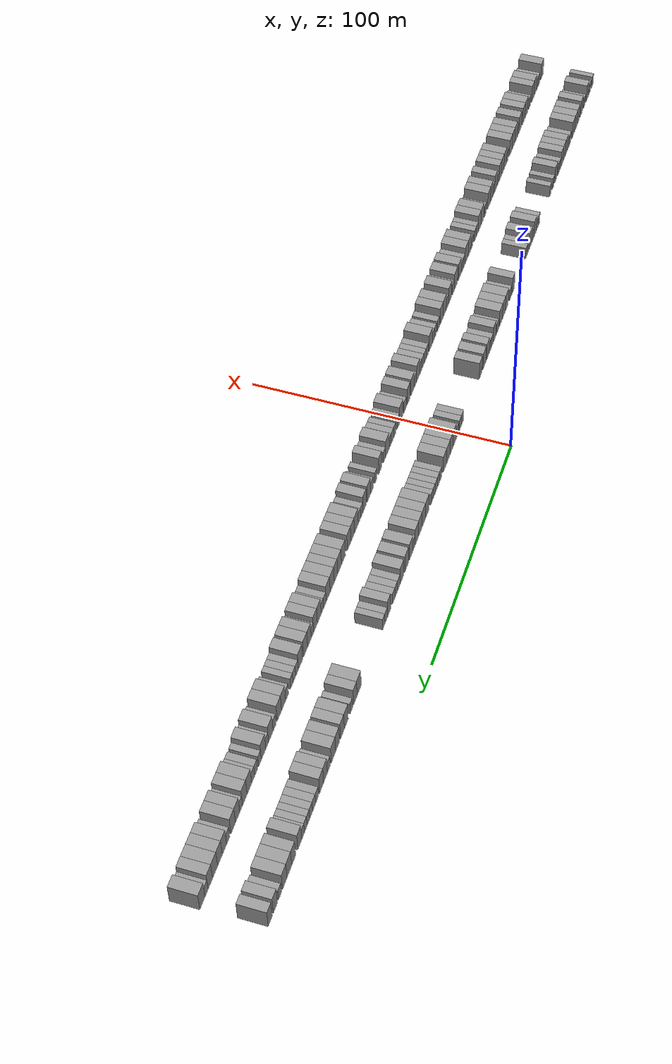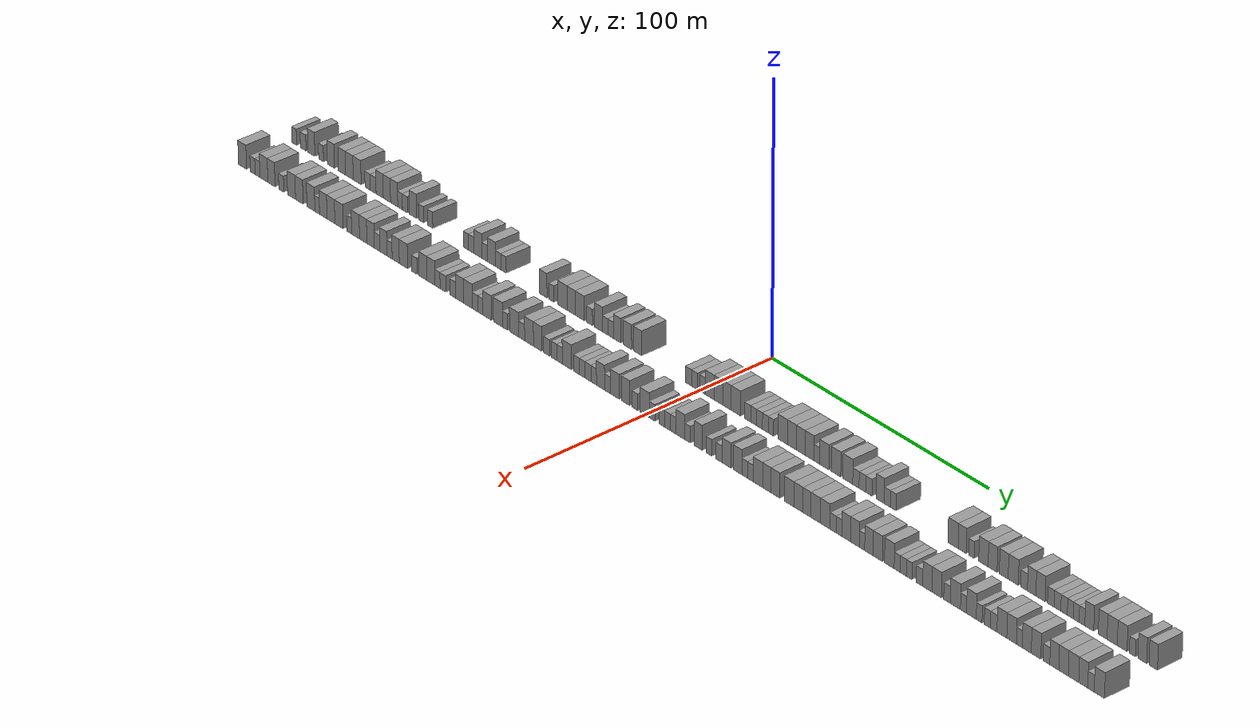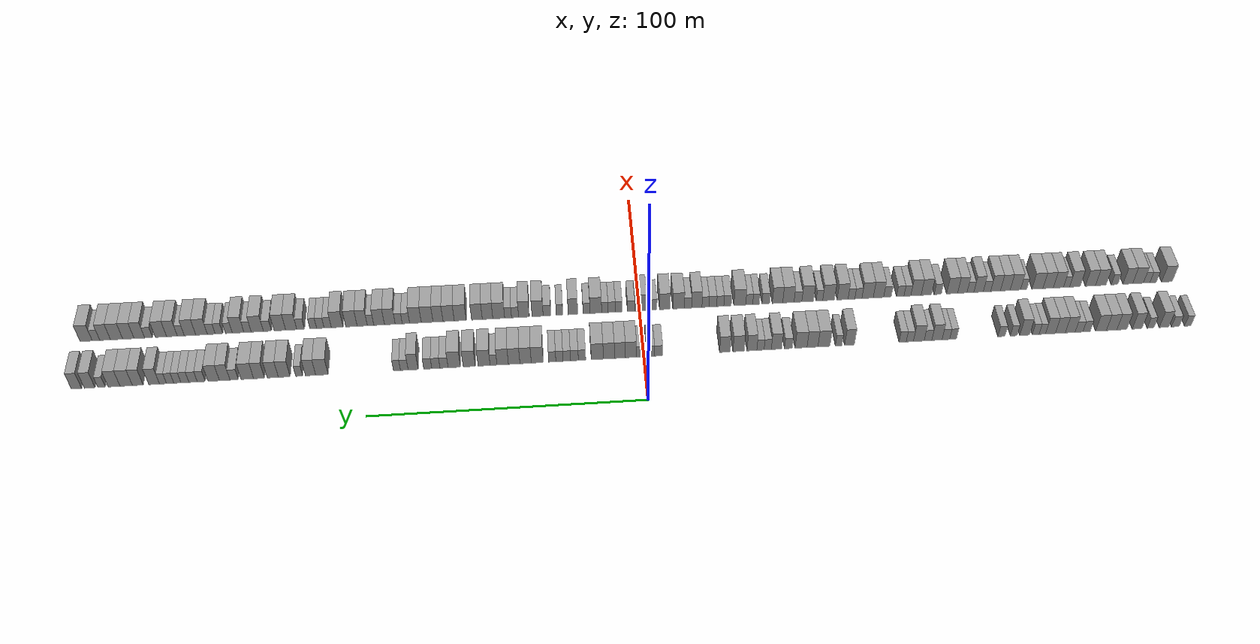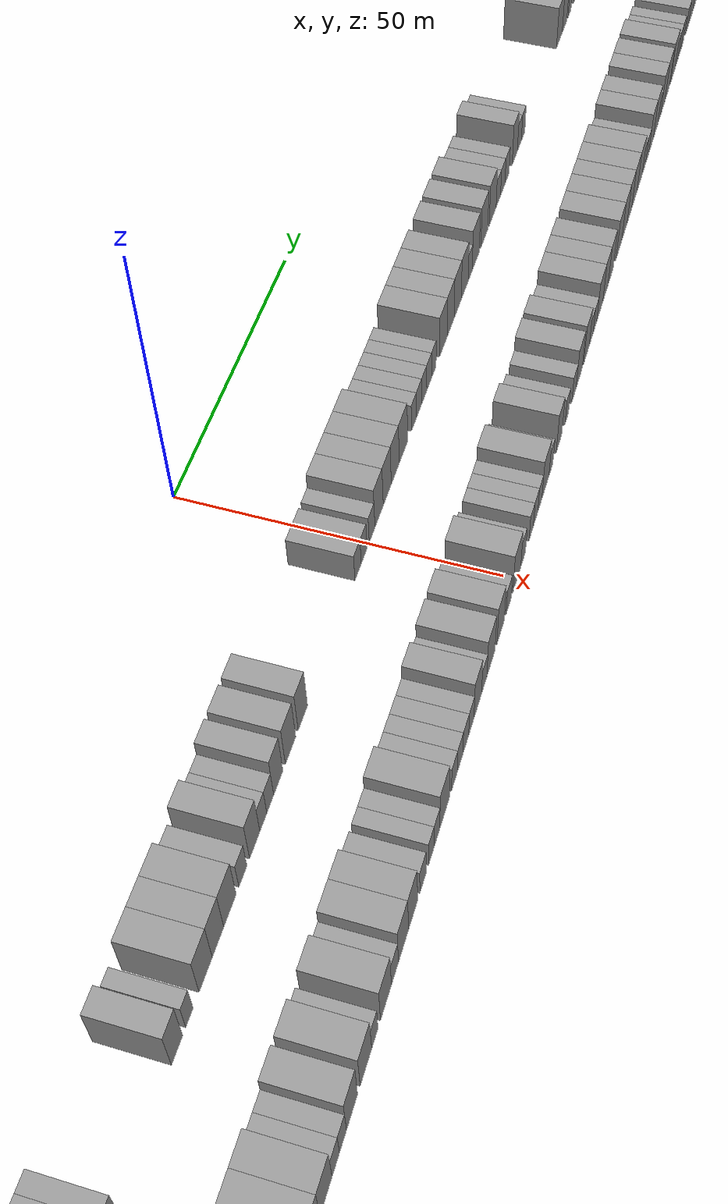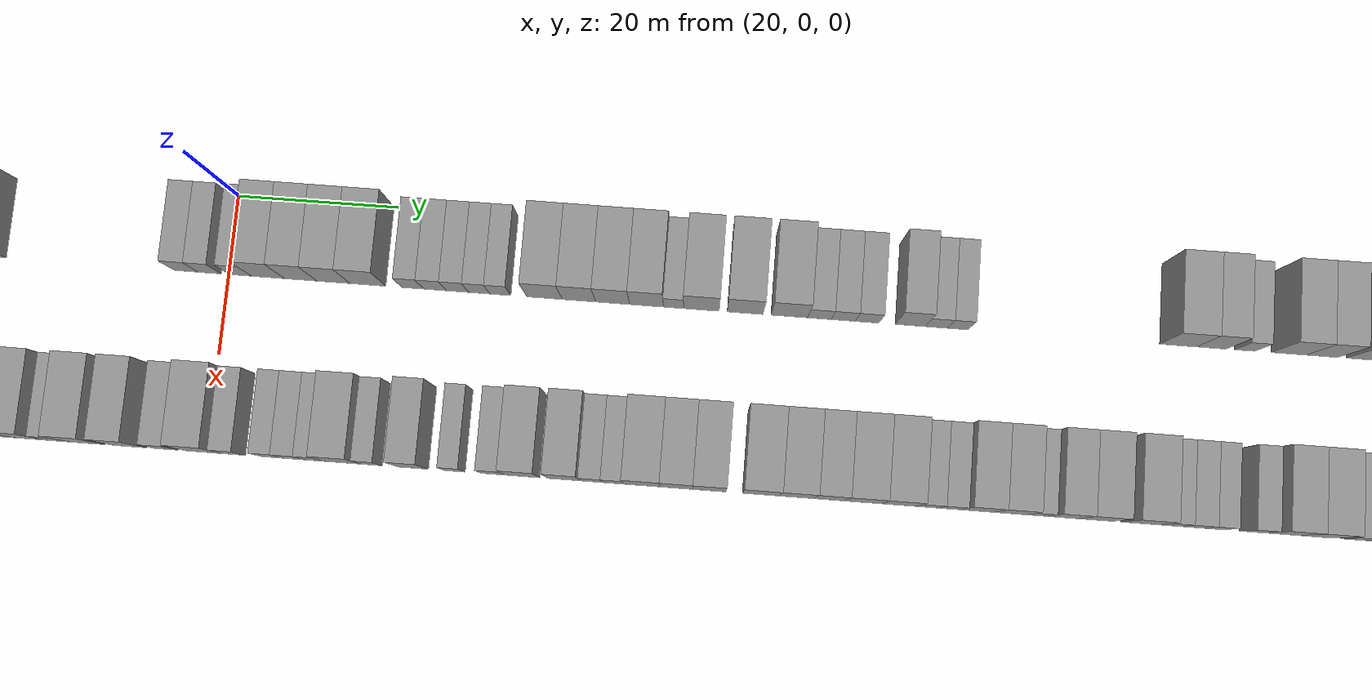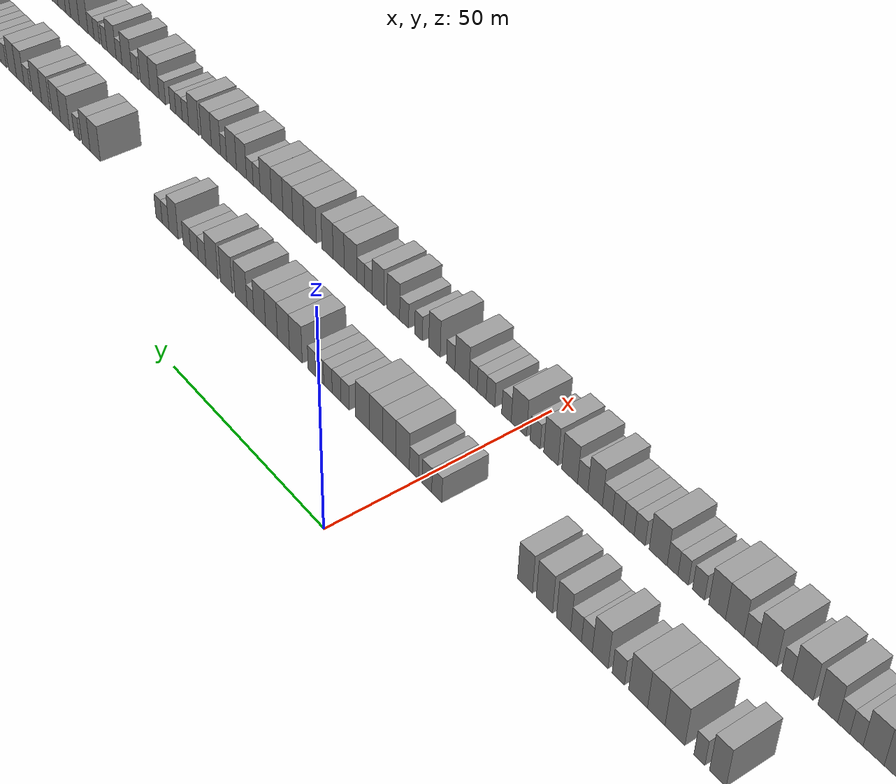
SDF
<sdf version="1.6">
 <world name="default">
  <scene>
   <sky><clouds><speed>12</speed></clouds></sky>
   <ambient>0.4 0.4 0.4 1</ambient>
   <background>0.7 0.7 0.7 1</background>
   <shadows>1</shadows>
  </scene>
  <gravity>0 0 -9.8066</gravity>
  <magnetic_field>6e-06 2.3e-05 -4.2e-05</magnetic_field>
  <physics default="0" name="default_physics" type="ode">
   <ode>
    <solver>
     <type>quick</type>
     <iters>10</iters>
     <sor>1.0</sor>
     <use_dynamic_moi_rescaling>0</use_dynamic_moi_rescaling>
    </solver>
    <constraints>
     <cfm>0</cfm>
     <erp>0.2</erp>
     <contact_max_correcting_vel>100</contact_max_correcting_vel>
     <contact_surface_layer>0.001</contact_surface_layer>
    </constraints>
   </ode>
   <max_step_size>0.004</max_step_size>
   <real_time_factor>1</real_time_factor>
   <real_time_update_rate>250</real_time_update_rate>
  </physics>
  <light name="sun" type="directional">
   <pose>0 0 10 0 0 0</pose>
   <diffuse>0.8 0.8 0.8 1</diffuse>
   <specular>0.2 0.2 0.2 1</specular>
   <attenuation>
    <range>1000</range>
    <constant>0.9</constant>
    <linear>0.01</linear>
    <quadratic>0.001</quadratic>
   </attenuation>
   <direction>-0.5 0.1 -0.9</direction>
  </light>
  <model name="building_1">
   <static>1</static>
   <pose>25.0000 -202.7742 0 0.000000 0.000000 0.000000</pose>
   <link name="link">
    <pose>0 0 3.00 0 0 0</pose>
    <collision name="collision"><geometry><box><size>10.0000 2.4517 6.0000</size></box></geometry></collision>
    <visual name="visual">
     <cast_shadows>0</cast_shadows>
     <geometry><box><size>10.0000 2.4517 6.0000</size></box></geometry>
     <material>
      <script>
       <uri>model://grey_wall/materials/scripts</uri>
       <uri>model://grey_wall/materials/textures</uri>
       <name>vrc/grey_wall</name>
      </script>
     </material>
    </visual>
   </link>
  </model>
  <model name="building_2">
   <static>1</static>
   <pose>25.0000 -198.0626 0 0.000000 0.000000 0.000000</pose>
   <link name="link">
    <pose>0 0 3.00 0 0 0</pose>
    <collision name="collision"><geometry><box><size>10.0000 2.9713 6.0000</size></box></geometry></collision>
    <visual name="visual">
     <cast_shadows>0</cast_shadows>
     <geometry><box><size>10.0000 2.9713 6.0000</size></box></geometry>
     <material>
      <script>
       <uri>model://grey_wall/materials/scripts</uri>
       <uri>model://grey_wall/materials/textures</uri>
       <name>vrc/grey_wall</name>
      </script>
     </material>
    </visual>
   </link>
  </model>
  <model name="building_3">
   <static>1</static>
   <pose>25.0000 -193.7579 0 0.000000 0.000000 0.000000</pose>
   <link name="link">
    <pose>0 0 4.50 0 0 0</pose>
    <collision name="collision"><geometry><box><size>10.0000 3.6382 9.0000</size></box></geometry></collision>
    <visual name="visual">
     <cast_shadows>0</cast_shadows>
     <geometry><box><size>10.0000 3.6382 9.0000</size></box></geometry>
     <material>
      <script>
       <uri>model://grey_wall/materials/scripts</uri>
       <uri>model://grey_wall/materials/textures</uri>
       <name>vrc/grey_wall</name>
      </script>
     </material>
    </visual>
   </link>
  </model>
  <model name="building_4">
   <static>1</static>
   <pose>25.0000 -188.6675 0 0.000000 0.000000 0.000000</pose>
   <link name="link">
    <pose>0 0 3.00 0 0 0</pose>
    <collision name="collision"><geometry><box><size>10.0000 2.5426 6.0000</size></box></geometry></collision>
    <visual name="visual">
     <cast_shadows>0</cast_shadows>
     <geometry><box><size>10.0000 2.5426 6.0000</size></box></geometry>
     <material>
      <script>
       <uri>model://grey_wall/materials/scripts</uri>
       <uri>model://grey_wall/materials/textures</uri>
       <name>vrc/grey_wall</name>
      </script>
     </material>
    </visual>
   </link>
  </model>
  <model name="building_5">
   <static>1</static>
   <pose>25.0000 -183.5469 0 0.000000 0.000000 0.000000</pose>
   <link name="link">
    <pose>0 0 4.50 0 0 0</pose>
    <collision name="collision"><geometry><box><size>10.0000 3.6987 9.0000</size></box></geometry></collision>
    <visual name="visual">
     <cast_shadows>0</cast_shadows>
     <geometry><box><size>10.0000 3.6987 9.0000</size></box></geometry>
     <material>
      <script>
       <uri>model://grey_wall/materials/scripts</uri>
       <uri>model://grey_wall/materials/textures</uri>
       <name>vrc/grey_wall</name>
      </script>
     </material>
    </visual>
   </link>
  </model>
  <model name="building_6">
   <static>1</static>
   <pose>25.0000 -177.7807 0 0.000000 0.000000 0.000000</pose>
   <link name="link">
    <pose>0 0 4.50 0 0 0</pose>
    <collision name="collision"><geometry><box><size>10.0000 3.8337 9.0000</size></box></geometry></collision>
    <visual name="visual">
     <cast_shadows>0</cast_shadows>
     <geometry><box><size>10.0000 3.8337 9.0000</size></box></geometry>
     <material>
      <script>
       <uri>model://grey_wall/materials/scripts</uri>
       <uri>model://grey_wall/materials/textures</uri>
       <name>vrc/grey_wall</name>
      </script>
     </material>
    </visual>
   </link>
  </model>
  <model name="building_7">
   <static>1</static>
   <pose>25.0000 -173.8962 0 0.000000 0.000000 0.000000</pose>
   <link name="link">
    <pose>0 0 4.50 0 0 0</pose>
    <collision name="collision"><geometry><box><size>10.0000 3.9352 9.0000</size></box></geometry></collision>
    <visual name="visual">
     <cast_shadows>0</cast_shadows>
     <geometry><box><size>10.0000 3.9352 9.0000</size></box></geometry>
     <material>
      <script>
       <uri>model://grey_wall/materials/scripts</uri>
       <uri>model://grey_wall/materials/textures</uri>
       <name>vrc/grey_wall</name>
      </script>
     </material>
    </visual>
   </link>
  </model>
  <model name="building_8">
   <static>1</static>
   <pose>25.0000 -169.8892 0 0.000000 0.000000 0.000000</pose>
   <link name="link">
    <pose>0 0 4.50 0 0 0</pose>
    <collision name="collision"><geometry><box><size>10.0000 4.0788 9.0000</size></box></geometry></collision>
    <visual name="visual">
     <cast_shadows>0</cast_shadows>
     <geometry><box><size>10.0000 4.0788 9.0000</size></box></geometry>
     <material>
      <script>
       <uri>model://grey_wall/materials/scripts</uri>
       <uri>model://grey_wall/materials/textures</uri>
       <name>vrc/grey_wall</name>
      </script>
     </material>
    </visual>
   </link>
  </model>
  <model name="building_9">
   <static>1</static>
   <pose>25.0000 -164.4599 0 0.000000 0.000000 0.000000</pose>
   <link name="link">
    <pose>0 0 3.00 0 0 0</pose>
    <collision name="collision"><geometry><box><size>10.0000 2.7798 6.0000</size></box></geometry></collision>
    <visual name="visual">
     <cast_shadows>0</cast_shadows>
     <geometry><box><size>10.0000 2.7798 6.0000</size></box></geometry>
     <material>
      <script>
       <uri>model://grey_wall/materials/scripts</uri>
       <uri>model://grey_wall/materials/textures</uri>
       <name>vrc/grey_wall</name>
      </script>
     </material>
    </visual>
   </link>
  </model>
  <model name="building_10">
   <static>1</static>
   <pose>25.0000 -161.5999 0 0.000000 0.000000 0.000000</pose>
   <link name="link">
    <pose>0 0 3.00 0 0 0</pose>
    <collision name="collision"><geometry><box><size>10.0000 2.9401 6.0000</size></box></geometry></collision>
    <visual name="visual">
     <cast_shadows>0</cast_shadows>
     <geometry><box><size>10.0000 2.9401 6.0000</size></box></geometry>
     <material>
      <script>
       <uri>model://grey_wall/materials/scripts</uri>
       <uri>model://grey_wall/materials/textures</uri>
       <name>vrc/grey_wall</name>
      </script>
     </material>
    </visual>
   </link>
  </model>
  <model name="building_11">
   <static>1</static>
   <pose>25.0000 -158.2807 0 0.000000 0.000000 0.000000</pose>
   <link name="link">
    <pose>0 0 4.50 0 0 0</pose>
    <collision name="collision"><geometry><box><size>10.0000 3.6983 9.0000</size></box></geometry></collision>
    <visual name="visual">
     <cast_shadows>0</cast_shadows>
     <geometry><box><size>10.0000 3.6983 9.0000</size></box></geometry>
     <material>
      <script>
       <uri>model://grey_wall/materials/scripts</uri>
       <uri>model://grey_wall/materials/textures</uri>
       <name>vrc/grey_wall</name>
      </script>
     </material>
    </visual>
   </link>
  </model>
  <model name="building_12">
   <static>1</static>
   <pose>25.0000 -154.5642 0 0.000000 0.000000 0.000000</pose>
   <link name="link">
    <pose>0 0 4.50 0 0 0</pose>
    <collision name="collision"><geometry><box><size>10.0000 3.7347 9.0000</size></box></geometry></collision>
    <visual name="visual">
     <cast_shadows>0</cast_shadows>
     <geometry><box><size>10.0000 3.7347 9.0000</size></box></geometry>
     <material>
      <script>
       <uri>model://grey_wall/materials/scripts</uri>
       <uri>model://grey_wall/materials/textures</uri>
       <name>vrc/grey_wall</name>
      </script>
     </material>
    </visual>
   </link>
  </model>
  <model name="building_13">
   <static>1</static>
   <pose>25.0000 -150.8454 0 0.000000 0.000000 0.000000</pose>
   <link name="link">
    <pose>0 0 4.50 0 0 0</pose>
    <collision name="collision"><geometry><box><size>10.0000 3.7028 9.0000</size></box></geometry></collision>
    <visual name="visual">
     <cast_shadows>0</cast_shadows>
     <geometry><box><size>10.0000 3.7028 9.0000</size></box></geometry>
     <material>
      <script>
       <uri>model://grey_wall/materials/scripts</uri>
       <uri>model://grey_wall/materials/textures</uri>
       <name>vrc/grey_wall</name>
      </script>
     </material>
    </visual>
   </link>
  </model>
  <model name="building_14">
   <static>1</static>
   <pose>25.0000 -147.7914 0 0.000000 0.000000 0.000000</pose>
   <link name="link">
    <pose>0 0 3.00 0 0 0</pose>
    <collision name="collision"><geometry><box><size>10.0000 2.4053 6.0000</size></box></geometry></collision>
    <visual name="visual">
     <cast_shadows>0</cast_shadows>
     <geometry><box><size>10.0000 2.4053 6.0000</size></box></geometry>
     <material>
      <script>
       <uri>model://grey_wall/materials/scripts</uri>
       <uri>model://grey_wall/materials/textures</uri>
       <name>vrc/grey_wall</name>
      </script>
     </material>
    </visual>
   </link>
  </model>
  <model name="building_15">
   <static>1</static>
   <pose>25.0000 -145.2952 0 0.000000 0.000000 0.000000</pose>
   <link name="link">
    <pose>0 0 3.00 0 0 0</pose>
    <collision name="collision"><geometry><box><size>10.0000 2.5870 6.0000</size></box></geometry></collision>
    <visual name="visual">
     <cast_shadows>0</cast_shadows>
     <geometry><box><size>10.0000 2.5870 6.0000</size></box></geometry>
     <material>
      <script>
       <uri>model://grey_wall/materials/scripts</uri>
       <uri>model://grey_wall/materials/textures</uri>
       <name>vrc/grey_wall</name>
      </script>
     </material>
    </visual>
   </link>
  </model>
  <model name="building_16">
   <static>1</static>
   <pose>25.0000 -141.1525 0 0.000000 0.000000 0.000000</pose>
   <link name="link">
    <pose>0 0 4.50 0 0 0</pose>
    <collision name="collision"><geometry><box><size>10.0000 3.6984 9.0000</size></box></geometry></collision>
    <visual name="visual">
     <cast_shadows>0</cast_shadows>
     <geometry><box><size>10.0000 3.6984 9.0000</size></box></geometry>
     <material>
      <script>
       <uri>model://grey_wall/materials/scripts</uri>
       <uri>model://grey_wall/materials/textures</uri>
       <name>vrc/grey_wall</name>
      </script>
     </material>
    </visual>
   </link>
  </model>
  <model name="building_17">
   <static>1</static>
   <pose>25.0000 -137.0269 0 0.000000 0.000000 0.000000</pose>
   <link name="link">
    <pose>0 0 3.00 0 0 0</pose>
    <collision name="collision"><geometry><box><size>10.0000 2.5526 6.0000</size></box></geometry></collision>
    <visual name="visual">
     <cast_shadows>0</cast_shadows>
     <geometry><box><size>10.0000 2.5526 6.0000</size></box></geometry>
     <material>
      <script>
       <uri>model://grey_wall/materials/scripts</uri>
       <uri>model://grey_wall/materials/textures</uri>
       <name>vrc/grey_wall</name>
      </script>
     </material>
    </visual>
   </link>
  </model>
  <model name="building_18">
   <static>1</static>
   <pose>25.0000 -132.4183 0 0.000000 0.000000 0.000000</pose>
   <link name="link">
    <pose>0 0 3.00 0 0 0</pose>
    <collision name="collision"><geometry><box><size>10.0000 2.6648 6.0000</size></box></geometry></collision>
    <visual name="visual">
     <cast_shadows>0</cast_shadows>
     <geometry><box><size>10.0000 2.6648 6.0000</size></box></geometry>
     <material>
      <script>
       <uri>model://grey_wall/materials/scripts</uri>
       <uri>model://grey_wall/materials/textures</uri>
       <name>vrc/grey_wall</name>
      </script>
     </material>
    </visual>
   </link>
  </model>
  <model name="building_19">
   <static>1</static>
   <pose>25.0000 -114.2712 0 0.000000 0.000000 0.000000</pose>
   <link name="link">
    <pose>0 0 3.00 0 0 0</pose>
    <collision name="collision"><geometry><box><size>10.0000 2.5431 6.0000</size></box></geometry></collision>
    <visual name="visual">
     <cast_shadows>0</cast_shadows>
     <geometry><box><size>10.0000 2.5431 6.0000</size></box></geometry>
     <material>
      <script>
       <uri>model://grey_wall/materials/scripts</uri>
       <uri>model://grey_wall/materials/textures</uri>
       <name>vrc/grey_wall</name>
      </script>
     </material>
    </visual>
   </link>
  </model>
  <model name="building_20">
   <static>1</static>
   <pose>25.0000 -111.5728 0 0.000000 0.000000 0.000000</pose>
   <link name="link">
    <pose>0 0 3.00 0 0 0</pose>
    <collision name="collision"><geometry><box><size>10.0000 2.8536 6.0000</size></box></geometry></collision>
    <visual name="visual">
     <cast_shadows>0</cast_shadows>
     <geometry><box><size>10.0000 2.8536 6.0000</size></box></geometry>
     <material>
      <script>
       <uri>model://grey_wall/materials/scripts</uri>
       <uri>model://grey_wall/materials/textures</uri>
       <name>vrc/grey_wall</name>
      </script>
     </material>
    </visual>
   </link>
  </model>
  <model name="building_21">
   <static>1</static>
   <pose>25.0000 -108.2441 0 0.000000 0.000000 0.000000</pose>
   <link name="link">
    <pose>0 0 4.50 0 0 0</pose>
    <collision name="collision"><geometry><box><size>10.0000 3.8039 9.0000</size></box></geometry></collision>
    <visual name="visual">
     <cast_shadows>0</cast_shadows>
     <geometry><box><size>10.0000 3.8039 9.0000</size></box></geometry>
     <material>
      <script>
       <uri>model://grey_wall/materials/scripts</uri>
       <uri>model://grey_wall/materials/textures</uri>
       <name>vrc/grey_wall</name>
      </script>
     </material>
    </visual>
   </link>
  </model>
  <model name="building_22">
   <static>1</static>
   <pose>25.0000 -104.9059 0 0.000000 0.000000 0.000000</pose>
   <link name="link">
    <pose>0 0 3.00 0 0 0</pose>
    <collision name="collision"><geometry><box><size>10.0000 2.8725 6.0000</size></box></geometry></collision>
    <visual name="visual">
     <cast_shadows>0</cast_shadows>
     <geometry><box><size>10.0000 2.8725 6.0000</size></box></geometry>
     <material>
      <script>
       <uri>model://grey_wall/materials/scripts</uri>
       <uri>model://grey_wall/materials/textures</uri>
       <name>vrc/grey_wall</name>
      </script>
     </material>
    </visual>
   </link>
  </model>
  <model name="building_23">
   <static>1</static>
   <pose>25.0000 -101.4643 0 0.000000 0.000000 0.000000</pose>
   <link name="link">
    <pose>0 0 4.50 0 0 0</pose>
    <collision name="collision"><geometry><box><size>10.0000 4.0108 9.0000</size></box></geometry></collision>
    <visual name="visual">
     <cast_shadows>0</cast_shadows>
     <geometry><box><size>10.0000 4.0108 9.0000</size></box></geometry>
     <material>
      <script>
       <uri>model://grey_wall/materials/scripts</uri>
       <uri>model://grey_wall/materials/textures</uri>
       <name>vrc/grey_wall</name>
      </script>
     </material>
    </visual>
   </link>
  </model>
  <model name="building_24">
   <static>1</static>
   <pose>25.0000 -98.1248 0 0.000000 0.000000 0.000000</pose>
   <link name="link">
    <pose>0 0 3.00 0 0 0</pose>
    <collision name="collision"><geometry><box><size>10.0000 2.6683 6.0000</size></box></geometry></collision>
    <visual name="visual">
     <cast_shadows>0</cast_shadows>
     <geometry><box><size>10.0000 2.6683 6.0000</size></box></geometry>
     <material>
      <script>
       <uri>model://grey_wall/materials/scripts</uri>
       <uri>model://grey_wall/materials/textures</uri>
       <name>vrc/grey_wall</name>
      </script>
     </material>
    </visual>
   </link>
  </model>
  <model name="building_25">
   <static>1</static>
   <pose>25.0000 -95.4521 0 0.000000 0.000000 0.000000</pose>
   <link name="link">
    <pose>0 0 3.00 0 0 0</pose>
    <collision name="collision"><geometry><box><size>10.0000 2.6770 6.0000</size></box></geometry></collision>
    <visual name="visual">
     <cast_shadows>0</cast_shadows>
     <geometry><box><size>10.0000 2.6770 6.0000</size></box></geometry>
     <material>
      <script>
       <uri>model://grey_wall/materials/scripts</uri>
       <uri>model://grey_wall/materials/textures</uri>
       <name>vrc/grey_wall</name>
      </script>
     </material>
    </visual>
   </link>
  </model>
  <model name="building_26">
   <static>1</static>
   <pose>25.0000 -75.6816 0 0.000000 0.000000 0.000000</pose>
   <link name="link">
    <pose>0 0 4.50 0 0 0</pose>
    <collision name="collision"><geometry><box><size>10.0000 3.6213 9.0000</size></box></geometry></collision>
    <visual name="visual">
     <cast_shadows>0</cast_shadows>
     <geometry><box><size>10.0000 3.6213 9.0000</size></box></geometry>
     <material>
      <script>
       <uri>model://grey_wall/materials/scripts</uri>
       <uri>model://grey_wall/materials/textures</uri>
       <name>vrc/grey_wall</name>
      </script>
     </material>
    </visual>
   </link>
  </model>
  <model name="building_27">
   <static>1</static>
   <pose>25.0000 -71.6547 0 0.000000 0.000000 0.000000</pose>
   <link name="link">
    <pose>0 0 3.00 0 0 0</pose>
    <collision name="collision"><geometry><box><size>10.0000 2.4325 6.0000</size></box></geometry></collision>
    <visual name="visual">
     <cast_shadows>0</cast_shadows>
     <geometry><box><size>10.0000 2.4325 6.0000</size></box></geometry>
     <material>
      <script>
       <uri>model://grey_wall/materials/scripts</uri>
       <uri>model://grey_wall/materials/textures</uri>
       <name>vrc/grey_wall</name>
      </script>
     </material>
    </visual>
   </link>
  </model>
  <model name="building_28">
   <static>1</static>
   <pose>25.0000 -66.1913 0 0.000000 0.000000 0.000000</pose>
   <link name="link">
    <pose>0 0 4.50 0 0 0</pose>
    <collision name="collision"><geometry><box><size>10.0000 4.4942 9.0000</size></box></geometry></collision>
    <visual name="visual">
     <cast_shadows>0</cast_shadows>
     <geometry><box><size>10.0000 4.4942 9.0000</size></box></geometry>
     <material>
      <script>
       <uri>model://grey_wall/materials/scripts</uri>
       <uri>model://grey_wall/materials/textures</uri>
       <name>vrc/grey_wall</name>
      </script>
     </material>
    </visual>
   </link>
  </model>
  <model name="building_29">
   <static>1</static>
   <pose>25.0000 -61.9204 0 0.000000 0.000000 0.000000</pose>
   <link name="link">
    <pose>0 0 4.50 0 0 0</pose>
    <collision name="collision"><geometry><box><size>10.0000 4.0477 9.0000</size></box></geometry></collision>
    <visual name="visual">
     <cast_shadows>0</cast_shadows>
     <geometry><box><size>10.0000 4.0477 9.0000</size></box></geometry>
     <material>
      <script>
       <uri>model://grey_wall/materials/scripts</uri>
       <uri>model://grey_wall/materials/textures</uri>
       <name>vrc/grey_wall</name>
      </script>
     </material>
    </visual>
   </link>
  </model>
  <model name="building_30">
   <static>1</static>
   <pose>25.0000 -57.6876 0 0.000000 0.000000 0.000000</pose>
   <link name="link">
    <pose>0 0 4.50 0 0 0</pose>
    <collision name="collision"><geometry><box><size>10.0000 4.4179 9.0000</size></box></geometry></collision>
    <visual name="visual">
     <cast_shadows>0</cast_shadows>
     <geometry><box><size>10.0000 4.4179 9.0000</size></box></geometry>
     <material>
      <script>
       <uri>model://grey_wall/materials/scripts</uri>
       <uri>model://grey_wall/materials/textures</uri>
       <name>vrc/grey_wall</name>
      </script>
     </material>
    </visual>
   </link>
  </model>
  <model name="building_31">
   <static>1</static>
   <pose>25.0000 -53.0100 0 0.000000 0.000000 0.000000</pose>
   <link name="link">
    <pose>0 0 3.00 0 0 0</pose>
    <collision name="collision"><geometry><box><size>10.0000 2.9374 6.0000</size></box></geometry></collision>
    <visual name="visual">
     <cast_shadows>0</cast_shadows>
     <geometry><box><size>10.0000 2.9374 6.0000</size></box></geometry>
     <material>
      <script>
       <uri>model://grey_wall/materials/scripts</uri>
       <uri>model://grey_wall/materials/textures</uri>
       <name>vrc/grey_wall</name>
      </script>
     </material>
    </visual>
   </link>
  </model>
  <model name="building_32">
   <static>1</static>
   <pose>25.0000 -48.6133 0 0.000000 0.000000 0.000000</pose>
   <link name="link">
    <pose>0 0 4.50 0 0 0</pose>
    <collision name="collision"><geometry><box><size>10.0000 3.8559 9.0000</size></box></geometry></collision>
    <visual name="visual">
     <cast_shadows>0</cast_shadows>
     <geometry><box><size>10.0000 3.8559 9.0000</size></box></geometry>
     <material>
      <script>
       <uri>model://grey_wall/materials/scripts</uri>
       <uri>model://grey_wall/materials/textures</uri>
       <name>vrc/grey_wall</name>
      </script>
     </material>
    </visual>
   </link>
  </model>
  <model name="building_33">
   <static>1</static>
   <pose>25.0000 -45.3594 0 0.000000 0.000000 0.000000</pose>
   <link name="link">
    <pose>0 0 3.00 0 0 0</pose>
    <collision name="collision"><geometry><box><size>10.0000 2.6521 6.0000</size></box></geometry></collision>
    <visual name="visual">
     <cast_shadows>0</cast_shadows>
     <geometry><box><size>10.0000 2.6521 6.0000</size></box></geometry>
     <material>
      <script>
       <uri>model://grey_wall/materials/scripts</uri>
       <uri>model://grey_wall/materials/textures</uri>
       <name>vrc/grey_wall</name>
      </script>
     </material>
    </visual>
   </link>
  </model>
  <model name="building_34">
   <static>1</static>
   <pose>25.0000 -42.6899 0 0.000000 0.000000 0.000000</pose>
   <link name="link">
    <pose>0 0 3.00 0 0 0</pose>
    <collision name="collision"><geometry><box><size>10.0000 2.6868 6.0000</size></box></geometry></collision>
    <visual name="visual">
     <cast_shadows>0</cast_shadows>
     <geometry><box><size>10.0000 2.6868 6.0000</size></box></geometry>
     <material>
      <script>
       <uri>model://grey_wall/materials/scripts</uri>
       <uri>model://grey_wall/materials/textures</uri>
       <name>vrc/grey_wall</name>
      </script>
     </material>
    </visual>
   </link>
  </model>
  <model name="building_35">
   <static>1</static>
   <pose>25.0000 -39.5424 0 0.000000 0.000000 0.000000</pose>
   <link name="link">
    <pose>0 0 4.50 0 0 0</pose>
    <collision name="collision"><geometry><box><size>10.0000 3.6082 9.0000</size></box></geometry></collision>
    <visual name="visual">
     <cast_shadows>0</cast_shadows>
     <geometry><box><size>10.0000 3.6082 9.0000</size></box></geometry>
     <material>
      <script>
       <uri>model://grey_wall/materials/scripts</uri>
       <uri>model://grey_wall/materials/textures</uri>
       <name>vrc/grey_wall</name>
      </script>
     </material>
    </visual>
   </link>
  </model>
  <model name="building_36">
   <static>1</static>
   <pose>25.0000 -34.6428 0 0.000000 0.000000 0.000000</pose>
   <link name="link">
    <pose>0 0 4.50 0 0 0</pose>
    <collision name="collision"><geometry><box><size>10.0000 4.1911 9.0000</size></box></geometry></collision>
    <visual name="visual">
     <cast_shadows>0</cast_shadows>
     <geometry><box><size>10.0000 4.1911 9.0000</size></box></geometry>
     <material>
      <script>
       <uri>model://grey_wall/materials/scripts</uri>
       <uri>model://grey_wall/materials/textures</uri>
       <name>vrc/grey_wall</name>
      </script>
     </material>
    </visual>
   </link>
  </model>
  <model name="building_37">
   <static>1</static>
   <pose>25.0000 -29.5987 0 0.000000 0.000000 0.000000</pose>
   <link name="link">
    <pose>0 0 4.50 0 0 0</pose>
    <collision name="collision"><geometry><box><size>10.0000 3.8973 9.0000</size></box></geometry></collision>
    <visual name="visual">
     <cast_shadows>0</cast_shadows>
     <geometry><box><size>10.0000 3.8973 9.0000</size></box></geometry>
     <material>
      <script>
       <uri>model://grey_wall/materials/scripts</uri>
       <uri>model://grey_wall/materials/textures</uri>
       <name>vrc/grey_wall</name>
      </script>
     </material>
    </visual>
   </link>
  </model>
  <model name="building_38">
   <static>1</static>
   <pose>25.0000 -5.2154 0 0.000000 0.000000 0.000000</pose>
   <link name="link">
    <pose>0 0 3.00 0 0 0</pose>
    <collision name="collision"><geometry><box><size>10.0000 2.9564 6.0000</size></box></geometry></collision>
    <visual name="visual">
     <cast_shadows>0</cast_shadows>
     <geometry><box><size>10.0000 2.9564 6.0000</size></box></geometry>
     <material>
      <script>
       <uri>model://grey_wall/materials/scripts</uri>
       <uri>model://grey_wall/materials/textures</uri>
       <name>vrc/grey_wall</name>
      </script>
     </material>
    </visual>
   </link>
  </model>
  <model name="building_39">
   <static>1</static>
   <pose>25.0000 -2.3277 0 0.000000 0.000000 0.000000</pose>
   <link name="link">
    <pose>0 0 3.00 0 0 0</pose>
    <collision name="collision"><geometry><box><size>10.0000 2.8189 6.0000</size></box></geometry></collision>
    <visual name="visual">
     <cast_shadows>0</cast_shadows>
     <geometry><box><size>10.0000 2.8189 6.0000</size></box></geometry>
     <material>
      <script>
       <uri>model://grey_wall/materials/scripts</uri>
       <uri>model://grey_wall/materials/textures</uri>
       <name>vrc/grey_wall</name>
      </script>
     </material>
    </visual>
   </link>
  </model>
  <model name="building_40">
   <static>1</static>
   <pose>25.0000 1.4617 0 0.000000 0.000000 0.000000</pose>
   <link name="link">
    <pose>0 0 3.00 0 0 0</pose>
    <collision name="collision"><geometry><box><size>10.0000 2.7599 6.0000</size></box></geometry></collision>
    <visual name="visual">
     <cast_shadows>0</cast_shadows>
     <geometry><box><size>10.0000 2.7599 6.0000</size></box></geometry>
     <material>
      <script>
       <uri>model://grey_wall/materials/scripts</uri>
       <uri>model://grey_wall/materials/textures</uri>
       <name>vrc/grey_wall</name>
      </script>
     </material>
    </visual>
   </link>
  </model>
  <model name="building_41">
   <static>1</static>
   <pose>25.0000 4.8905 0 0.000000 0.000000 0.000000</pose>
   <link name="link">
    <pose>0 0 4.50 0 0 0</pose>
    <collision name="collision"><geometry><box><size>10.0000 4.0977 9.0000</size></box></geometry></collision>
    <visual name="visual">
     <cast_shadows>0</cast_shadows>
     <geometry><box><size>10.0000 4.0977 9.0000</size></box></geometry>
     <material>
      <script>
       <uri>model://grey_wall/materials/scripts</uri>
       <uri>model://grey_wall/materials/textures</uri>
       <name>vrc/grey_wall</name>
      </script>
     </material>
    </visual>
   </link>
  </model>
  <model name="building_42">
   <static>1</static>
   <pose>25.0000 8.9445 0 0.000000 0.000000 0.000000</pose>
   <link name="link">
    <pose>0 0 4.50 0 0 0</pose>
    <collision name="collision"><geometry><box><size>10.0000 4.0104 9.0000</size></box></geometry></collision>
    <visual name="visual">
     <cast_shadows>0</cast_shadows>
     <geometry><box><size>10.0000 4.0104 9.0000</size></box></geometry>
     <material>
      <script>
       <uri>model://grey_wall/materials/scripts</uri>
       <uri>model://grey_wall/materials/textures</uri>
       <name>vrc/grey_wall</name>
      </script>
     </material>
    </visual>
   </link>
  </model>
  <model name="building_43">
   <static>1</static>
   <pose>25.0000 12.9975 0 0.000000 0.000000 0.000000</pose>
   <link name="link">
    <pose>0 0 4.50 0 0 0</pose>
    <collision name="collision"><geometry><box><size>10.0000 4.0955 9.0000</size></box></geometry></collision>
    <visual name="visual">
     <cast_shadows>0</cast_shadows>
     <geometry><box><size>10.0000 4.0955 9.0000</size></box></geometry>
     <material>
      <script>
       <uri>model://grey_wall/materials/scripts</uri>
       <uri>model://grey_wall/materials/textures</uri>
       <name>vrc/grey_wall</name>
      </script>
     </material>
    </visual>
   </link>
  </model>
  <model name="building_44">
   <static>1</static>
   <pose>25.0000 17.2449 0 0.000000 0.000000 0.000000</pose>
   <link name="link">
    <pose>0 0 4.50 0 0 0</pose>
    <collision name="collision"><geometry><box><size>10.0000 4.3993 9.0000</size></box></geometry></collision>
    <visual name="visual">
     <cast_shadows>0</cast_shadows>
     <geometry><box><size>10.0000 4.3993 9.0000</size></box></geometry>
     <material>
      <script>
       <uri>model://grey_wall/materials/scripts</uri>
       <uri>model://grey_wall/materials/textures</uri>
       <name>vrc/grey_wall</name>
      </script>
     </material>
    </visual>
   </link>
  </model>
  <model name="building_45">
   <static>1</static>
   <pose>25.0000 22.7931 0 0.000000 0.000000 0.000000</pose>
   <link name="link">
    <pose>0 0 3.00 0 0 0</pose>
    <collision name="collision"><geometry><box><size>10.0000 2.6971 6.0000</size></box></geometry></collision>
    <visual name="visual">
     <cast_shadows>0</cast_shadows>
     <geometry><box><size>10.0000 2.6971 6.0000</size></box></geometry>
     <material>
      <script>
       <uri>model://grey_wall/materials/scripts</uri>
       <uri>model://grey_wall/materials/textures</uri>
       <name>vrc/grey_wall</name>
      </script>
     </material>
    </visual>
   </link>
  </model>
  <model name="building_46">
   <static>1</static>
   <pose>25.0000 25.5501 0 0.000000 0.000000 0.000000</pose>
   <link name="link">
    <pose>0 0 3.00 0 0 0</pose>
    <collision name="collision"><geometry><box><size>10.0000 2.8170 6.0000</size></box></geometry></collision>
    <visual name="visual">
     <cast_shadows>0</cast_shadows>
     <geometry><box><size>10.0000 2.8170 6.0000</size></box></geometry>
     <material>
      <script>
       <uri>model://grey_wall/materials/scripts</uri>
       <uri>model://grey_wall/materials/textures</uri>
       <name>vrc/grey_wall</name>
      </script>
     </material>
    </visual>
   </link>
  </model>
  <model name="building_47">
   <static>1</static>
   <pose>25.0000 28.3322 0 0.000000 0.000000 0.000000</pose>
   <link name="link">
    <pose>0 0 3.00 0 0 0</pose>
    <collision name="collision"><geometry><box><size>10.0000 2.7472 6.0000</size></box></geometry></collision>
    <visual name="visual">
     <cast_shadows>0</cast_shadows>
     <geometry><box><size>10.0000 2.7472 6.0000</size></box></geometry>
     <material>
      <script>
       <uri>model://grey_wall/materials/scripts</uri>
       <uri>model://grey_wall/materials/textures</uri>
       <name>vrc/grey_wall</name>
      </script>
     </material>
    </visual>
   </link>
  </model>
  <model name="building_48">
   <static>1</static>
   <pose>25.0000 31.0269 0 0.000000 0.000000 0.000000</pose>
   <link name="link">
    <pose>0 0 3.00 0 0 0</pose>
    <collision name="collision"><geometry><box><size>10.0000 2.6422 6.0000</size></box></geometry></collision>
    <visual name="visual">
     <cast_shadows>0</cast_shadows>
     <geometry><box><size>10.0000 2.6422 6.0000</size></box></geometry>
     <material>
      <script>
       <uri>model://grey_wall/materials/scripts</uri>
       <uri>model://grey_wall/materials/textures</uri>
       <name>vrc/grey_wall</name>
      </script>
     </material>
    </visual>
   </link>
  </model>
  <model name="building_49">
   <static>1</static>
   <pose>25.0000 33.6311 0 0.000000 0.000000 0.000000</pose>
   <link name="link">
    <pose>0 0 3.00 0 0 0</pose>
    <collision name="collision"><geometry><box><size>10.0000 2.5661 6.0000</size></box></geometry></collision>
    <visual name="visual">
     <cast_shadows>0</cast_shadows>
     <geometry><box><size>10.0000 2.5661 6.0000</size></box></geometry>
     <material>
      <script>
       <uri>model://grey_wall/materials/scripts</uri>
       <uri>model://grey_wall/materials/textures</uri>
       <name>vrc/grey_wall</name>
      </script>
     </material>
    </visual>
   </link>
  </model>
  <model name="building_50">
   <static>1</static>
   <pose>25.0000 39.0998 0 0.000000 0.000000 0.000000</pose>
   <link name="link">
    <pose>0 0 4.50 0 0 0</pose>
    <collision name="collision"><geometry><box><size>10.0000 4.3714 9.0000</size></box></geometry></collision>
    <visual name="visual">
     <cast_shadows>0</cast_shadows>
     <geometry><box><size>10.0000 4.3714 9.0000</size></box></geometry>
     <material>
      <script>
       <uri>model://grey_wall/materials/scripts</uri>
       <uri>model://grey_wall/materials/textures</uri>
       <name>vrc/grey_wall</name>
      </script>
     </material>
    </visual>
   </link>
  </model>
  <model name="building_51">
   <static>1</static>
   <pose>25.0000 43.3485 0 0.000000 0.000000 0.000000</pose>
   <link name="link">
    <pose>0 0 4.50 0 0 0</pose>
    <collision name="collision"><geometry><box><size>10.0000 4.1260 9.0000</size></box></geometry></collision>
    <visual name="visual">
     <cast_shadows>0</cast_shadows>
     <geometry><box><size>10.0000 4.1260 9.0000</size></box></geometry>
     <material>
      <script>
       <uri>model://grey_wall/materials/scripts</uri>
       <uri>model://grey_wall/materials/textures</uri>
       <name>vrc/grey_wall</name>
      </script>
     </material>
    </visual>
   </link>
  </model>
  <model name="building_52">
   <static>1</static>
   <pose>25.0000 47.5089 0 0.000000 0.000000 0.000000</pose>
   <link name="link">
    <pose>0 0 4.50 0 0 0</pose>
    <collision name="collision"><geometry><box><size>10.0000 4.1948 9.0000</size></box></geometry></collision>
    <visual name="visual">
     <cast_shadows>0</cast_shadows>
     <geometry><box><size>10.0000 4.1948 9.0000</size></box></geometry>
     <material>
      <script>
       <uri>model://grey_wall/materials/scripts</uri>
       <uri>model://grey_wall/materials/textures</uri>
       <name>vrc/grey_wall</name>
      </script>
     </material>
    </visual>
   </link>
  </model>
  <model name="building_53">
   <static>1</static>
   <pose>25.0000 51.6875 0 0.000000 0.000000 0.000000</pose>
   <link name="link">
    <pose>0 0 4.50 0 0 0</pose>
    <collision name="collision"><geometry><box><size>10.0000 4.1624 9.0000</size></box></geometry></collision>
    <visual name="visual">
     <cast_shadows>0</cast_shadows>
     <geometry><box><size>10.0000 4.1624 9.0000</size></box></geometry>
     <material>
      <script>
       <uri>model://grey_wall/materials/scripts</uri>
       <uri>model://grey_wall/materials/textures</uri>
       <name>vrc/grey_wall</name>
      </script>
     </material>
    </visual>
   </link>
  </model>
  <model name="building_54">
   <static>1</static>
   <pose>25.0000 55.0041 0 0.000000 0.000000 0.000000</pose>
   <link name="link">
    <pose>0 0 3.00 0 0 0</pose>
    <collision name="collision"><geometry><box><size>10.0000 2.4706 6.0000</size></box></geometry></collision>
    <visual name="visual">
     <cast_shadows>0</cast_shadows>
     <geometry><box><size>10.0000 2.4706 6.0000</size></box></geometry>
     <material>
      <script>
       <uri>model://grey_wall/materials/scripts</uri>
       <uri>model://grey_wall/materials/textures</uri>
       <name>vrc/grey_wall</name>
      </script>
     </material>
    </visual>
   </link>
  </model>
  <model name="building_55">
   <static>1</static>
   <pose>25.0000 58.4217 0 0.000000 0.000000 0.000000</pose>
   <link name="link">
    <pose>0 0 4.50 0 0 0</pose>
    <collision name="collision"><geometry><box><size>10.0000 4.3647 9.0000</size></box></geometry></collision>
    <visual name="visual">
     <cast_shadows>0</cast_shadows>
     <geometry><box><size>10.0000 4.3647 9.0000</size></box></geometry>
     <material>
      <script>
       <uri>model://grey_wall/materials/scripts</uri>
       <uri>model://grey_wall/materials/textures</uri>
       <name>vrc/grey_wall</name>
      </script>
     </material>
    </visual>
   </link>
  </model>
  <model name="building_56">
   <static>1</static>
   <pose>25.0000 63.7967 0 0.000000 0.000000 0.000000</pose>
   <link name="link">
    <pose>0 0 4.50 0 0 0</pose>
    <collision name="collision"><geometry><box><size>10.0000 4.3852 9.0000</size></box></geometry></collision>
    <visual name="visual">
     <cast_shadows>0</cast_shadows>
     <geometry><box><size>10.0000 4.3852 9.0000</size></box></geometry>
     <material>
      <script>
       <uri>model://grey_wall/materials/scripts</uri>
       <uri>model://grey_wall/materials/textures</uri>
       <name>vrc/grey_wall</name>
      </script>
     </material>
    </visual>
   </link>
  </model>
  <model name="building_57">
   <static>1</static>
   <pose>25.0000 69.2320 0 0.000000 0.000000 0.000000</pose>
   <link name="link">
    <pose>0 0 4.50 0 0 0</pose>
    <collision name="collision"><geometry><box><size>10.0000 4.4853 9.0000</size></box></geometry></collision>
    <visual name="visual">
     <cast_shadows>0</cast_shadows>
     <geometry><box><size>10.0000 4.4853 9.0000</size></box></geometry>
     <material>
      <script>
       <uri>model://grey_wall/materials/scripts</uri>
       <uri>model://grey_wall/materials/textures</uri>
       <name>vrc/grey_wall</name>
      </script>
     </material>
    </visual>
   </link>
  </model>
  <model name="building_58">
   <static>1</static>
   <pose>25.0000 72.9330 0 0.000000 0.000000 0.000000</pose>
   <link name="link">
    <pose>0 0 3.00 0 0 0</pose>
    <collision name="collision"><geometry><box><size>10.0000 2.9168 6.0000</size></box></geometry></collision>
    <visual name="visual">
     <cast_shadows>0</cast_shadows>
     <geometry><box><size>10.0000 2.9168 6.0000</size></box></geometry>
     <material>
      <script>
       <uri>model://grey_wall/materials/scripts</uri>
       <uri>model://grey_wall/materials/textures</uri>
       <name>vrc/grey_wall</name>
      </script>
     </material>
    </visual>
   </link>
  </model>
  <model name="building_59">
   <static>1</static>
   <pose>25.0000 75.8683 0 0.000000 0.000000 0.000000</pose>
   <link name="link">
    <pose>0 0 3.00 0 0 0</pose>
    <collision name="collision"><geometry><box><size>10.0000 2.9537 6.0000</size></box></geometry></collision>
    <visual name="visual">
     <cast_shadows>0</cast_shadows>
     <geometry><box><size>10.0000 2.9537 6.0000</size></box></geometry>
     <material>
      <script>
       <uri>model://grey_wall/materials/scripts</uri>
       <uri>model://grey_wall/materials/textures</uri>
       <name>vrc/grey_wall</name>
      </script>
     </material>
    </visual>
   </link>
  </model>
  <model name="building_60">
   <static>1</static>
   <pose>25.0000 78.8032 0 0.000000 0.000000 0.000000</pose>
   <link name="link">
    <pose>0 0 3.00 0 0 0</pose>
    <collision name="collision"><geometry><box><size>10.0000 2.9161 6.0000</size></box></geometry></collision>
    <visual name="visual">
     <cast_shadows>0</cast_shadows>
     <geometry><box><size>10.0000 2.9161 6.0000</size></box></geometry>
     <material>
      <script>
       <uri>model://grey_wall/materials/scripts</uri>
       <uri>model://grey_wall/materials/textures</uri>
       <name>vrc/grey_wall</name>
      </script>
     </material>
    </visual>
   </link>
  </model>
  <model name="building_61">
   <static>1</static>
   <pose>25.0000 84.0866 0 0.000000 0.000000 0.000000</pose>
   <link name="link">
    <pose>0 0 4.50 0 0 0</pose>
    <collision name="collision"><geometry><box><size>10.0000 3.6506 9.0000</size></box></geometry></collision>
    <visual name="visual">
     <cast_shadows>0</cast_shadows>
     <geometry><box><size>10.0000 3.6506 9.0000</size></box></geometry>
     <material>
      <script>
       <uri>model://grey_wall/materials/scripts</uri>
       <uri>model://grey_wall/materials/textures</uri>
       <name>vrc/grey_wall</name>
      </script>
     </material>
    </visual>
   </link>
  </model>
  <model name="building_62">
   <static>1</static>
   <pose>25.0000 87.2775 0 0.000000 0.000000 0.000000</pose>
   <link name="link">
    <pose>0 0 3.00 0 0 0</pose>
    <collision name="collision"><geometry><box><size>10.0000 2.7312 6.0000</size></box></geometry></collision>
    <visual name="visual">
     <cast_shadows>0</cast_shadows>
     <geometry><box><size>10.0000 2.7312 6.0000</size></box></geometry>
     <material>
      <script>
       <uri>model://grey_wall/materials/scripts</uri>
       <uri>model://grey_wall/materials/textures</uri>
       <name>vrc/grey_wall</name>
      </script>
     </material>
    </visual>
   </link>
  </model>
  <model name="building_63">
   <static>1</static>
   <pose>25.0000 89.9140 0 0.000000 0.000000 0.000000</pose>
   <link name="link">
    <pose>0 0 3.00 0 0 0</pose>
    <collision name="collision"><geometry><box><size>10.0000 2.5418 6.0000</size></box></geometry></collision>
    <visual name="visual">
     <cast_shadows>0</cast_shadows>
     <geometry><box><size>10.0000 2.5418 6.0000</size></box></geometry>
     <material>
      <script>
       <uri>model://grey_wall/materials/scripts</uri>
       <uri>model://grey_wall/materials/textures</uri>
       <name>vrc/grey_wall</name>
      </script>
     </material>
    </visual>
   </link>
  </model>
  <model name="building_64">
   <static>1</static>
   <pose>25.0000 116.9255 0 0.000000 0.000000 0.000000</pose>
   <link name="link">
    <pose>0 0 4.50 0 0 0</pose>
    <collision name="collision"><geometry><box><size>10.0000 4.4937 9.0000</size></box></geometry></collision>
    <visual name="visual">
     <cast_shadows>0</cast_shadows>
     <geometry><box><size>10.0000 4.4937 9.0000</size></box></geometry>
     <material>
      <script>
       <uri>model://grey_wall/materials/scripts</uri>
       <uri>model://grey_wall/materials/textures</uri>
       <name>vrc/grey_wall</name>
      </script>
     </material>
    </visual>
   </link>
  </model>
  <model name="building_65">
   <static>1</static>
   <pose>25.0000 121.0052 0 0.000000 0.000000 0.000000</pose>
   <link name="link">
    <pose>0 0 4.50 0 0 0</pose>
    <collision name="collision"><geometry><box><size>10.0000 3.6657 9.0000</size></box></geometry></collision>
    <visual name="visual">
     <cast_shadows>0</cast_shadows>
     <geometry><box><size>10.0000 3.6657 9.0000</size></box></geometry>
     <material>
      <script>
       <uri>model://grey_wall/materials/scripts</uri>
       <uri>model://grey_wall/materials/textures</uri>
       <name>vrc/grey_wall</name>
      </script>
     </material>
    </visual>
   </link>
  </model>
  <model name="building_66">
   <static>1</static>
   <pose>25.0000 125.0866 0 0.000000 0.000000 0.000000</pose>
   <link name="link">
    <pose>0 0 3.00 0 0 0</pose>
    <collision name="collision"><geometry><box><size>10.0000 2.4970 6.0000</size></box></geometry></collision>
    <visual name="visual">
     <cast_shadows>0</cast_shadows>
     <geometry><box><size>10.0000 2.4970 6.0000</size></box></geometry>
     <material>
      <script>
       <uri>model://grey_wall/materials/scripts</uri>
       <uri>model://grey_wall/materials/textures</uri>
       <name>vrc/grey_wall</name>
      </script>
     </material>
    </visual>
   </link>
  </model>
  <model name="building_67">
   <static>1</static>
   <pose>25.0000 130.4352 0 0.000000 0.000000 0.000000</pose>
   <link name="link">
    <pose>0 0 4.50 0 0 0</pose>
    <collision name="collision"><geometry><box><size>10.0000 4.2004 9.0000</size></box></geometry></collision>
    <visual name="visual">
     <cast_shadows>0</cast_shadows>
     <geometry><box><size>10.0000 4.2004 9.0000</size></box></geometry>
     <material>
      <script>
       <uri>model://grey_wall/materials/scripts</uri>
       <uri>model://grey_wall/materials/textures</uri>
       <name>vrc/grey_wall</name>
      </script>
     </material>
    </visual>
   </link>
  </model>
  <model name="building_68">
   <static>1</static>
   <pose>25.0000 134.5130 0 0.000000 0.000000 0.000000</pose>
   <link name="link">
    <pose>0 0 4.50 0 0 0</pose>
    <collision name="collision"><geometry><box><size>10.0000 3.9551 9.0000</size></box></geometry></collision>
    <visual name="visual">
     <cast_shadows>0</cast_shadows>
     <geometry><box><size>10.0000 3.9551 9.0000</size></box></geometry>
     <material>
      <script>
       <uri>model://grey_wall/materials/scripts</uri>
       <uri>model://grey_wall/materials/textures</uri>
       <name>vrc/grey_wall</name>
      </script>
     </material>
    </visual>
   </link>
  </model>
  <model name="building_69">
   <static>1</static>
   <pose>25.0000 139.4348 0 0.000000 0.000000 0.000000</pose>
   <link name="link">
    <pose>0 0 4.50 0 0 0</pose>
    <collision name="collision"><geometry><box><size>10.0000 3.8885 9.0000</size></box></geometry></collision>
    <visual name="visual">
     <cast_shadows>0</cast_shadows>
     <geometry><box><size>10.0000 3.8885 9.0000</size></box></geometry>
     <material>
      <script>
       <uri>model://grey_wall/materials/scripts</uri>
       <uri>model://grey_wall/materials/textures</uri>
       <name>vrc/grey_wall</name>
      </script>
     </material>
    </visual>
   </link>
  </model>
  <model name="building_70">
   <static>1</static>
   <pose>25.0000 143.6241 0 0.000000 0.000000 0.000000</pose>
   <link name="link">
    <pose>0 0 4.50 0 0 0</pose>
    <collision name="collision"><geometry><box><size>10.0000 4.4902 9.0000</size></box></geometry></collision>
    <visual name="visual">
     <cast_shadows>0</cast_shadows>
     <geometry><box><size>10.0000 4.4902 9.0000</size></box></geometry>
     <material>
      <script>
       <uri>model://grey_wall/materials/scripts</uri>
       <uri>model://grey_wall/materials/textures</uri>
       <name>vrc/grey_wall</name>
      </script>
     </material>
    </visual>
   </link>
  </model>
  <model name="building_71">
   <static>1</static>
   <pose>25.0000 148.3583 0 0.000000 0.000000 0.000000</pose>
   <link name="link">
    <pose>0 0 3.00 0 0 0</pose>
    <collision name="collision"><geometry><box><size>10.0000 2.9782 6.0000</size></box></geometry></collision>
    <visual name="visual">
     <cast_shadows>0</cast_shadows>
     <geometry><box><size>10.0000 2.9782 6.0000</size></box></geometry>
     <material>
      <script>
       <uri>model://grey_wall/materials/scripts</uri>
       <uri>model://grey_wall/materials/textures</uri>
       <name>vrc/grey_wall</name>
      </script>
     </material>
    </visual>
   </link>
  </model>
  <model name="building_72">
   <static>1</static>
   <pose>25.0000 151.7246 0 0.000000 0.000000 0.000000</pose>
   <link name="link">
    <pose>0 0 4.50 0 0 0</pose>
    <collision name="collision"><geometry><box><size>10.0000 3.7546 9.0000</size></box></geometry></collision>
    <visual name="visual">
     <cast_shadows>0</cast_shadows>
     <geometry><box><size>10.0000 3.7546 9.0000</size></box></geometry>
     <material>
      <script>
       <uri>model://grey_wall/materials/scripts</uri>
       <uri>model://grey_wall/materials/textures</uri>
       <name>vrc/grey_wall</name>
      </script>
     </material>
    </visual>
   </link>
  </model>
  <model name="building_73">
   <static>1</static>
   <pose>25.0000 155.6228 0 0.000000 0.000000 0.000000</pose>
   <link name="link">
    <pose>0 0 4.50 0 0 0</pose>
    <collision name="collision"><geometry><box><size>10.0000 4.0418 9.0000</size></box></geometry></collision>
    <visual name="visual">
     <cast_shadows>0</cast_shadows>
     <geometry><box><size>10.0000 4.0418 9.0000</size></box></geometry>
     <material>
      <script>
       <uri>model://grey_wall/materials/scripts</uri>
       <uri>model://grey_wall/materials/textures</uri>
       <name>vrc/grey_wall</name>
      </script>
     </material>
    </visual>
   </link>
  </model>
  <model name="building_74">
   <static>1</static>
   <pose>25.0000 160.0553 0 0.000000 0.000000 0.000000</pose>
   <link name="link">
    <pose>0 0 3.00 0 0 0</pose>
    <collision name="collision"><geometry><box><size>10.0000 2.8232 6.0000</size></box></geometry></collision>
    <visual name="visual">
     <cast_shadows>0</cast_shadows>
     <geometry><box><size>10.0000 2.8232 6.0000</size></box></geometry>
     <material>
      <script>
       <uri>model://grey_wall/materials/scripts</uri>
       <uri>model://grey_wall/materials/textures</uri>
       <name>vrc/grey_wall</name>
      </script>
     </material>
    </visual>
   </link>
  </model>
  <model name="building_75">
   <static>1</static>
   <pose>25.0000 162.9661 0 0.000000 0.000000 0.000000</pose>
   <link name="link">
    <pose>0 0 3.00 0 0 0</pose>
    <collision name="collision"><geometry><box><size>10.0000 2.9983 6.0000</size></box></geometry></collision>
    <visual name="visual">
     <cast_shadows>0</cast_shadows>
     <geometry><box><size>10.0000 2.9983 6.0000</size></box></geometry>
     <material>
      <script>
       <uri>model://grey_wall/materials/scripts</uri>
       <uri>model://grey_wall/materials/textures</uri>
       <name>vrc/grey_wall</name>
      </script>
     </material>
    </visual>
   </link>
  </model>
  <model name="building_76">
   <static>1</static>
   <pose>25.0000 165.8763 0 0.000000 0.000000 0.000000</pose>
   <link name="link">
    <pose>0 0 3.00 0 0 0</pose>
    <collision name="collision"><geometry><box><size>10.0000 2.8222 6.0000</size></box></geometry></collision>
    <visual name="visual">
     <cast_shadows>0</cast_shadows>
     <geometry><box><size>10.0000 2.8222 6.0000</size></box></geometry>
     <material>
      <script>
       <uri>model://grey_wall/materials/scripts</uri>
       <uri>model://grey_wall/materials/textures</uri>
       <name>vrc/grey_wall</name>
      </script>
     </material>
    </visual>
   </link>
  </model>
  <model name="building_77">
   <static>1</static>
   <pose>25.0000 168.5528 0 0.000000 0.000000 0.000000</pose>
   <link name="link">
    <pose>0 0 3.00 0 0 0</pose>
    <collision name="collision"><geometry><box><size>10.0000 2.5307 6.0000</size></box></geometry></collision>
    <visual name="visual">
     <cast_shadows>0</cast_shadows>
     <geometry><box><size>10.0000 2.5307 6.0000</size></box></geometry>
     <material>
      <script>
       <uri>model://grey_wall/materials/scripts</uri>
       <uri>model://grey_wall/materials/textures</uri>
       <name>vrc/grey_wall</name>
      </script>
     </material>
    </visual>
   </link>
  </model>
  <model name="building_78">
   <static>1</static>
   <pose>25.0000 171.1189 0 0.000000 0.000000 0.000000</pose>
   <link name="link">
    <pose>0 0 3.00 0 0 0</pose>
    <collision name="collision"><geometry><box><size>10.0000 2.6015 6.0000</size></box></geometry></collision>
    <visual name="visual">
     <cast_shadows>0</cast_shadows>
     <geometry><box><size>10.0000 2.6015 6.0000</size></box></geometry>
     <material>
      <script>
       <uri>model://grey_wall/materials/scripts</uri>
       <uri>model://grey_wall/materials/textures</uri>
       <name>vrc/grey_wall</name>
      </script>
     </material>
    </visual>
   </link>
  </model>
  <model name="building_79">
   <static>1</static>
   <pose>25.0000 173.6603 0 0.000000 0.000000 0.000000</pose>
   <link name="link">
    <pose>0 0 3.00 0 0 0</pose>
    <collision name="collision"><geometry><box><size>10.0000 2.4813 6.0000</size></box></geometry></collision>
    <visual name="visual">
     <cast_shadows>0</cast_shadows>
     <geometry><box><size>10.0000 2.4813 6.0000</size></box></geometry>
     <material>
      <script>
       <uri>model://grey_wall/materials/scripts</uri>
       <uri>model://grey_wall/materials/textures</uri>
       <name>vrc/grey_wall</name>
      </script>
     </material>
    </visual>
   </link>
  </model>
  <model name="building_80">
   <static>1</static>
   <pose>25.0000 176.8106 0 0.000000 0.000000 0.000000</pose>
   <link name="link">
    <pose>0 0 4.50 0 0 0</pose>
    <collision name="collision"><geometry><box><size>10.0000 3.8193 9.0000</size></box></geometry></collision>
    <visual name="visual">
     <cast_shadows>0</cast_shadows>
     <geometry><box><size>10.0000 3.8193 9.0000</size></box></geometry>
     <material>
      <script>
       <uri>model://grey_wall/materials/scripts</uri>
       <uri>model://grey_wall/materials/textures</uri>
       <name>vrc/grey_wall</name>
      </script>
     </material>
    </visual>
   </link>
  </model>
  <model name="building_81">
   <static>1</static>
   <pose>25.0000 182.6180 0 0.000000 0.000000 0.000000</pose>
   <link name="link">
    <pose>0 0 4.50 0 0 0</pose>
    <collision name="collision"><geometry><box><size>10.0000 3.7956 9.0000</size></box></geometry></collision>
    <visual name="visual">
     <cast_shadows>0</cast_shadows>
     <geometry><box><size>10.0000 3.7956 9.0000</size></box></geometry>
     <material>
      <script>
       <uri>model://grey_wall/materials/scripts</uri>
       <uri>model://grey_wall/materials/textures</uri>
       <name>vrc/grey_wall</name>
      </script>
     </material>
    </visual>
   </link>
  </model>
  <model name="building_82">
   <static>1</static>
   <pose>25.0000 186.7122 0 0.000000 0.000000 0.000000</pose>
   <link name="link">
    <pose>0 0 4.50 0 0 0</pose>
    <collision name="collision"><geometry><box><size>10.0000 4.3926 9.0000</size></box></geometry></collision>
    <visual name="visual">
     <cast_shadows>0</cast_shadows>
     <geometry><box><size>10.0000 4.3926 9.0000</size></box></geometry>
     <material>
      <script>
       <uri>model://grey_wall/materials/scripts</uri>
       <uri>model://grey_wall/materials/textures</uri>
       <name>vrc/grey_wall</name>
      </script>
     </material>
    </visual>
   </link>
  </model>
  <model name="building_83">
   <static>1</static>
   <pose>25.0000 191.0016 0 0.000000 0.000000 0.000000</pose>
   <link name="link">
    <pose>0 0 4.50 0 0 0</pose>
    <collision name="collision"><geometry><box><size>10.0000 4.1864 9.0000</size></box></geometry></collision>
    <visual name="visual">
     <cast_shadows>0</cast_shadows>
     <geometry><box><size>10.0000 4.1864 9.0000</size></box></geometry>
     <material>
      <script>
       <uri>model://grey_wall/materials/scripts</uri>
       <uri>model://grey_wall/materials/textures</uri>
       <name>vrc/grey_wall</name>
      </script>
     </material>
    </visual>
   </link>
  </model>
  <model name="building_84">
   <static>1</static>
   <pose>25.0000 195.4252 0 0.000000 0.000000 0.000000</pose>
   <link name="link">
    <pose>0 0 3.00 0 0 0</pose>
    <collision name="collision"><geometry><box><size>10.0000 2.6609 6.0000</size></box></geometry></collision>
    <visual name="visual">
     <cast_shadows>0</cast_shadows>
     <geometry><box><size>10.0000 2.6609 6.0000</size></box></geometry>
     <material>
      <script>
       <uri>model://grey_wall/materials/scripts</uri>
       <uri>model://grey_wall/materials/textures</uri>
       <name>vrc/grey_wall</name>
      </script>
     </material>
    </visual>
   </link>
  </model>
  <model name="building_85">
   <static>1</static>
   <pose>25.0000 199.6288 0 0.000000 0.000000 0.000000</pose>
   <link name="link">
    <pose>0 0 4.50 0 0 0</pose>
    <collision name="collision"><geometry><box><size>10.0000 3.7462 9.0000</size></box></geometry></collision>
    <visual name="visual">
     <cast_shadows>0</cast_shadows>
     <geometry><box><size>10.0000 3.7462 9.0000</size></box></geometry>
     <material>
      <script>
       <uri>model://grey_wall/materials/scripts</uri>
       <uri>model://grey_wall/materials/textures</uri>
       <name>vrc/grey_wall</name>
      </script>
     </material>
    </visual>
   </link>
  </model>
  <model name="building_86">
   <static>1</static>
   <pose>25.0000 204.3061 0 0.000000 0.000000 0.000000</pose>
   <link name="link">
    <pose>0 0 4.50 0 0 0</pose>
    <collision name="collision"><geometry><box><size>10.0000 3.6085 9.0000</size></box></geometry></collision>
    <visual name="visual">
     <cast_shadows>0</cast_shadows>
     <geometry><box><size>10.0000 3.6085 9.0000</size></box></geometry>
     <material>
      <script>
       <uri>model://grey_wall/materials/scripts</uri>
       <uri>model://grey_wall/materials/textures</uri>
       <name>vrc/grey_wall</name>
      </script>
     </material>
    </visual>
   </link>
  </model>
  <model name="building_87">
   <static>1</static>
   <pose>47.0000 -201.8964 0 0.000000 0.000000 0.000000</pose>
   <link name="link">
    <pose>0 0 4.50 0 0 0</pose>
    <collision name="collision"><geometry><box><size>10.0000 4.2072 9.0000</size></box></geometry></collision>
    <visual name="visual">
     <cast_shadows>0</cast_shadows>
     <geometry><box><size>10.0000 4.2072 9.0000</size></box></geometry>
     <material>
      <script>
       <uri>model://grey_wall/materials/scripts</uri>
       <uri>model://grey_wall/materials/textures</uri>
       <name>vrc/grey_wall</name>
      </script>
     </material>
    </visual>
   </link>
  </model>
  <model name="building_88">
   <static>1</static>
   <pose>47.0000 -196.5256 0 0.000000 0.000000 0.000000</pose>
   <link name="link">
    <pose>0 0 3.00 0 0 0</pose>
    <collision name="collision"><geometry><box><size>10.0000 2.5345 6.0000</size></box></geometry></collision>
    <visual name="visual">
     <cast_shadows>0</cast_shadows>
     <geometry><box><size>10.0000 2.5345 6.0000</size></box></geometry>
     <material>
      <script>
       <uri>model://grey_wall/materials/scripts</uri>
       <uri>model://grey_wall/materials/textures</uri>
       <name>vrc/grey_wall</name>
      </script>
     </material>
    </visual>
   </link>
  </model>
  <model name="building_89">
   <static>1</static>
   <pose>47.0000 -193.9909 0 0.000000 0.000000 0.000000</pose>
   <link name="link">
    <pose>0 0 3.00 0 0 0</pose>
    <collision name="collision"><geometry><box><size>10.0000 2.5350 6.0000</size></box></geometry></collision>
    <visual name="visual">
     <cast_shadows>0</cast_shadows>
     <geometry><box><size>10.0000 2.5350 6.0000</size></box></geometry>
     <material>
      <script>
       <uri>model://grey_wall/materials/scripts</uri>
       <uri>model://grey_wall/materials/textures</uri>
       <name>vrc/grey_wall</name>
      </script>
     </material>
    </visual>
   </link>
  </model>
  <model name="building_90">
   <static>1</static>
   <pose>47.0000 -190.6429 0 0.000000 0.000000 0.000000</pose>
   <link name="link">
    <pose>0 0 4.50 0 0 0</pose>
    <collision name="collision"><geometry><box><size>10.0000 4.1609 9.0000</size></box></geometry></collision>
    <visual name="visual">
     <cast_shadows>0</cast_shadows>
     <geometry><box><size>10.0000 4.1609 9.0000</size></box></geometry>
     <material>
      <script>
       <uri>model://grey_wall/materials/scripts</uri>
       <uri>model://grey_wall/materials/textures</uri>
       <name>vrc/grey_wall</name>
      </script>
     </material>
    </visual>
   </link>
  </model>
  <model name="building_91">
   <static>1</static>
   <pose>47.0000 -186.6748 0 0.000000 0.000000 0.000000</pose>
   <link name="link">
    <pose>0 0 4.50 0 0 0</pose>
    <collision name="collision"><geometry><box><size>10.0000 3.7754 9.0000</size></box></geometry></collision>
    <visual name="visual">
     <cast_shadows>0</cast_shadows>
     <geometry><box><size>10.0000 3.7754 9.0000</size></box></geometry>
     <material>
      <script>
       <uri>model://grey_wall/materials/scripts</uri>
       <uri>model://grey_wall/materials/textures</uri>
       <name>vrc/grey_wall</name>
      </script>
     </material>
    </visual>
   </link>
  </model>
  <model name="building_92">
   <static>1</static>
   <pose>47.0000 -181.5037 0 0.000000 0.000000 0.000000</pose>
   <link name="link">
    <pose>0 0 3.00 0 0 0</pose>
    <collision name="collision"><geometry><box><size>10.0000 2.5666 6.0000</size></box></geometry></collision>
    <visual name="visual">
     <cast_shadows>0</cast_shadows>
     <geometry><box><size>10.0000 2.5666 6.0000</size></box></geometry>
     <material>
      <script>
       <uri>model://grey_wall/materials/scripts</uri>
       <uri>model://grey_wall/materials/textures</uri>
       <name>vrc/grey_wall</name>
      </script>
     </material>
    </visual>
   </link>
  </model>
  <model name="building_93">
   <static>1</static>
   <pose>47.0000 -176.1572 0 0.000000 0.000000 0.000000</pose>
   <link name="link">
    <pose>0 0 4.50 0 0 0</pose>
    <collision name="collision"><geometry><box><size>10.0000 4.1265 9.0000</size></box></geometry></collision>
    <visual name="visual">
     <cast_shadows>0</cast_shadows>
     <geometry><box><size>10.0000 4.1265 9.0000</size></box></geometry>
     <material>
      <script>
       <uri>model://grey_wall/materials/scripts</uri>
       <uri>model://grey_wall/materials/textures</uri>
       <name>vrc/grey_wall</name>
      </script>
     </material>
    </visual>
   </link>
  </model>
  <model name="building_94">
   <static>1</static>
   <pose>47.0000 -172.1310 0 0.000000 0.000000 0.000000</pose>
   <link name="link">
    <pose>0 0 4.50 0 0 0</pose>
    <collision name="collision"><geometry><box><size>10.0000 3.9259 9.0000</size></box></geometry></collision>
    <visual name="visual">
     <cast_shadows>0</cast_shadows>
     <geometry><box><size>10.0000 3.9259 9.0000</size></box></geometry>
     <material>
      <script>
       <uri>model://grey_wall/materials/scripts</uri>
       <uri>model://grey_wall/materials/textures</uri>
       <name>vrc/grey_wall</name>
      </script>
     </material>
    </visual>
   </link>
  </model>
  <model name="building_95">
   <static>1</static>
   <pose>47.0000 -166.1115 0 0.000000 0.000000 0.000000</pose>
   <link name="link">
    <pose>0 0 4.50 0 0 0</pose>
    <collision name="collision"><geometry><box><size>10.0000 4.1133 9.0000</size></box></geometry></collision>
    <visual name="visual">
     <cast_shadows>0</cast_shadows>
     <geometry><box><size>10.0000 4.1133 9.0000</size></box></geometry>
     <material>
      <script>
       <uri>model://grey_wall/materials/scripts</uri>
       <uri>model://grey_wall/materials/textures</uri>
       <name>vrc/grey_wall</name>
      </script>
     </material>
    </visual>
   </link>
  </model>
  <model name="building_96">
   <static>1</static>
   <pose>47.0000 -162.8544 0 0.000000 0.000000 0.000000</pose>
   <link name="link">
    <pose>0 0 3.00 0 0 0</pose>
    <collision name="collision"><geometry><box><size>10.0000 2.4008 6.0000</size></box></geometry></collision>
    <visual name="visual">
     <cast_shadows>0</cast_shadows>
     <geometry><box><size>10.0000 2.4008 6.0000</size></box></geometry>
     <material>
      <script>
       <uri>model://grey_wall/materials/scripts</uri>
       <uri>model://grey_wall/materials/textures</uri>
       <name>vrc/grey_wall</name>
      </script>
     </material>
    </visual>
   </link>
  </model>
  <model name="building_97">
   <static>1</static>
   <pose>47.0000 -159.7162 0 0.000000 0.000000 0.000000</pose>
   <link name="link">
    <pose>0 0 4.50 0 0 0</pose>
    <collision name="collision"><geometry><box><size>10.0000 3.8755 9.0000</size></box></geometry></collision>
    <visual name="visual">
     <cast_shadows>0</cast_shadows>
     <geometry><box><size>10.0000 3.8755 9.0000</size></box></geometry>
     <material>
      <script>
       <uri>model://grey_wall/materials/scripts</uri>
       <uri>model://grey_wall/materials/textures</uri>
       <name>vrc/grey_wall</name>
      </script>
     </material>
    </visual>
   </link>
  </model>
  <model name="building_98">
   <static>1</static>
   <pose>47.0000 -155.7651 0 0.000000 0.000000 0.000000</pose>
   <link name="link">
    <pose>0 0 4.50 0 0 0</pose>
    <collision name="collision"><geometry><box><size>10.0000 4.0269 9.0000</size></box></geometry></collision>
    <visual name="visual">
     <cast_shadows>0</cast_shadows>
     <geometry><box><size>10.0000 4.0269 9.0000</size></box></geometry>
     <material>
      <script>
       <uri>model://grey_wall/materials/scripts</uri>
       <uri>model://grey_wall/materials/textures</uri>
       <name>vrc/grey_wall</name>
      </script>
     </material>
    </visual>
   </link>
  </model>
  <model name="building_99">
   <static>1</static>
   <pose>47.0000 -151.6254 0 0.000000 0.000000 0.000000</pose>
   <link name="link">
    <pose>0 0 4.50 0 0 0</pose>
    <collision name="collision"><geometry><box><size>10.0000 4.2524 9.0000</size></box></geometry></collision>
    <visual name="visual">
     <cast_shadows>0</cast_shadows>
     <geometry><box><size>10.0000 4.2524 9.0000</size></box></geometry>
     <material>
      <script>
       <uri>model://grey_wall/materials/scripts</uri>
       <uri>model://grey_wall/materials/textures</uri>
       <name>vrc/grey_wall</name>
      </script>
     </material>
    </visual>
   </link>
  </model>
  <model name="building_100">
   <static>1</static>
   <pose>47.0000 -146.2927 0 0.000000 0.000000 0.000000</pose>
   <link name="link">
    <pose>0 0 3.00 0 0 0</pose>
    <collision name="collision"><geometry><box><size>10.0000 2.4131 6.0000</size></box></geometry></collision>
    <visual name="visual">
     <cast_shadows>0</cast_shadows>
     <geometry><box><size>10.0000 2.4131 6.0000</size></box></geometry>
     <material>
      <script>
       <uri>model://grey_wall/materials/scripts</uri>
       <uri>model://grey_wall/materials/textures</uri>
       <name>vrc/grey_wall</name>
      </script>
     </material>
    </visual>
   </link>
  </model>
  <model name="building_101">
   <static>1</static>
   <pose>47.0000 -143.0731 0 0.000000 0.000000 0.000000</pose>
   <link name="link">
    <pose>0 0 4.50 0 0 0</pose>
    <collision name="collision"><geometry><box><size>10.0000 4.0261 9.0000</size></box></geometry></collision>
    <visual name="visual">
     <cast_shadows>0</cast_shadows>
     <geometry><box><size>10.0000 4.0261 9.0000</size></box></geometry>
     <material>
      <script>
       <uri>model://grey_wall/materials/scripts</uri>
       <uri>model://grey_wall/materials/textures</uri>
       <name>vrc/grey_wall</name>
      </script>
     </material>
    </visual>
   </link>
  </model>
  <model name="building_102">
   <static>1</static>
   <pose>47.0000 -139.1915 0 0.000000 0.000000 0.000000</pose>
   <link name="link">
    <pose>0 0 4.50 0 0 0</pose>
    <collision name="collision"><geometry><box><size>10.0000 3.7372 9.0000</size></box></geometry></collision>
    <visual name="visual">
     <cast_shadows>0</cast_shadows>
     <geometry><box><size>10.0000 3.7372 9.0000</size></box></geometry>
     <material>
      <script>
       <uri>model://grey_wall/materials/scripts</uri>
       <uri>model://grey_wall/materials/textures</uri>
       <name>vrc/grey_wall</name>
      </script>
     </material>
    </visual>
   </link>
  </model>
  <model name="building_103">
   <static>1</static>
   <pose>47.0000 -135.4441 0 0.000000 0.000000 0.000000</pose>
   <link name="link">
    <pose>0 0 4.50 0 0 0</pose>
    <collision name="collision"><geometry><box><size>10.0000 3.7575 9.0000</size></box></geometry></collision>
    <visual name="visual">
     <cast_shadows>0</cast_shadows>
     <geometry><box><size>10.0000 3.7575 9.0000</size></box></geometry>
     <material>
      <script>
       <uri>model://grey_wall/materials/scripts</uri>
       <uri>model://grey_wall/materials/textures</uri>
       <name>vrc/grey_wall</name>
      </script>
     </material>
    </visual>
   </link>
  </model>
  <model name="building_104">
   <static>1</static>
   <pose>47.0000 -132.1372 0 0.000000 0.000000 0.000000</pose>
   <link name="link">
    <pose>0 0 3.00 0 0 0</pose>
    <collision name="collision"><geometry><box><size>10.0000 2.8563 6.0000</size></box></geometry></collision>
    <visual name="visual">
     <cast_shadows>0</cast_shadows>
     <geometry><box><size>10.0000 2.8563 6.0000</size></box></geometry>
     <material>
      <script>
       <uri>model://grey_wall/materials/scripts</uri>
       <uri>model://grey_wall/materials/textures</uri>
       <name>vrc/grey_wall</name>
      </script>
     </material>
    </visual>
   </link>
  </model>
  <model name="building_105">
   <static>1</static>
   <pose>47.0000 -128.9010 0 0.000000 0.000000 0.000000</pose>
   <link name="link">
    <pose>0 0 4.50 0 0 0</pose>
    <collision name="collision"><geometry><box><size>10.0000 3.6161 9.0000</size></box></geometry></collision>
    <visual name="visual">
     <cast_shadows>0</cast_shadows>
     <geometry><box><size>10.0000 3.6161 9.0000</size></box></geometry>
     <material>
      <script>
       <uri>model://grey_wall/materials/scripts</uri>
       <uri>model://grey_wall/materials/textures</uri>
       <name>vrc/grey_wall</name>
      </script>
     </material>
    </visual>
   </link>
  </model>
  <model name="building_106">
   <static>1</static>
   <pose>47.0000 -125.7627 0 0.000000 0.000000 0.000000</pose>
   <link name="link">
    <pose>0 0 3.00 0 0 0</pose>
    <collision name="collision"><geometry><box><size>10.0000 2.6606 6.0000</size></box></geometry></collision>
    <visual name="visual">
     <cast_shadows>0</cast_shadows>
     <geometry><box><size>10.0000 2.6606 6.0000</size></box></geometry>
     <material>
      <script>
       <uri>model://grey_wall/materials/scripts</uri>
       <uri>model://grey_wall/materials/textures</uri>
       <name>vrc/grey_wall</name>
      </script>
     </material>
    </visual>
   </link>
  </model>
  <model name="building_107">
   <static>1</static>
   <pose>47.0000 -122.6169 0 0.000000 0.000000 0.000000</pose>
   <link name="link">
    <pose>0 0 4.50 0 0 0</pose>
    <collision name="collision"><geometry><box><size>10.0000 3.6309 9.0000</size></box></geometry></collision>
    <visual name="visual">
     <cast_shadows>0</cast_shadows>
     <geometry><box><size>10.0000 3.6309 9.0000</size></box></geometry>
     <material>
      <script>
       <uri>model://grey_wall/materials/scripts</uri>
       <uri>model://grey_wall/materials/textures</uri>
       <name>vrc/grey_wall</name>
      </script>
     </material>
    </visual>
   </link>
  </model>
  <model name="building_108">
   <static>1</static>
   <pose>47.0000 -118.6958 0 0.000000 0.000000 0.000000</pose>
   <link name="link">
    <pose>0 0 4.50 0 0 0</pose>
    <collision name="collision"><geometry><box><size>10.0000 4.2112 9.0000</size></box></geometry></collision>
    <visual name="visual">
     <cast_shadows>0</cast_shadows>
     <geometry><box><size>10.0000 4.2112 9.0000</size></box></geometry>
     <material>
      <script>
       <uri>model://grey_wall/materials/scripts</uri>
       <uri>model://grey_wall/materials/textures</uri>
       <name>vrc/grey_wall</name>
      </script>
     </material>
    </visual>
   </link>
  </model>
  <model name="building_109">
   <static>1</static>
   <pose>47.0000 -113.2084 0 0.000000 0.000000 0.000000</pose>
   <link name="link">
    <pose>0 0 3.00 0 0 0</pose>
    <collision name="collision"><geometry><box><size>10.0000 2.7637 6.0000</size></box></geometry></collision>
    <visual name="visual">
     <cast_shadows>0</cast_shadows>
     <geometry><box><size>10.0000 2.7637 6.0000</size></box></geometry>
     <material>
      <script>
       <uri>model://grey_wall/materials/scripts</uri>
       <uri>model://grey_wall/materials/textures</uri>
       <name>vrc/grey_wall</name>
      </script>
     </material>
    </visual>
   </link>
  </model>
  <model name="building_110">
   <static>1</static>
   <pose>47.0000 -108.8260 0 0.000000 0.000000 0.000000</pose>
   <link name="link">
    <pose>0 0 4.50 0 0 0</pose>
    <collision name="collision"><geometry><box><size>10.0000 4.0009 9.0000</size></box></geometry></collision>
    <visual name="visual">
     <cast_shadows>0</cast_shadows>
     <geometry><box><size>10.0000 4.0009 9.0000</size></box></geometry>
     <material>
      <script>
       <uri>model://grey_wall/materials/scripts</uri>
       <uri>model://grey_wall/materials/textures</uri>
       <name>vrc/grey_wall</name>
      </script>
     </material>
    </visual>
   </link>
  </model>
  <model name="building_111">
   <static>1</static>
   <pose>47.0000 -104.8471 0 0.000000 0.000000 0.000000</pose>
   <link name="link">
    <pose>0 0 4.50 0 0 0</pose>
    <collision name="collision"><geometry><box><size>10.0000 3.9571 9.0000</size></box></geometry></collision>
    <visual name="visual">
     <cast_shadows>0</cast_shadows>
     <geometry><box><size>10.0000 3.9571 9.0000</size></box></geometry>
     <material>
      <script>
       <uri>model://grey_wall/materials/scripts</uri>
       <uri>model://grey_wall/materials/textures</uri>
       <name>vrc/grey_wall</name>
      </script>
     </material>
    </visual>
   </link>
  </model>
  <model name="building_112">
   <static>1</static>
   <pose>47.0000 -101.5576 0 0.000000 0.000000 0.000000</pose>
   <link name="link">
    <pose>0 0 3.00 0 0 0</pose>
    <collision name="collision"><geometry><box><size>10.0000 2.6218 6.0000</size></box></geometry></collision>
    <visual name="visual">
     <cast_shadows>0</cast_shadows>
     <geometry><box><size>10.0000 2.6218 6.0000</size></box></geometry>
     <material>
      <script>
       <uri>model://grey_wall/materials/scripts</uri>
       <uri>model://grey_wall/materials/textures</uri>
       <name>vrc/grey_wall</name>
      </script>
     </material>
    </visual>
   </link>
  </model>
  <model name="building_113">
   <static>1</static>
   <pose>47.0000 -98.8159 0 0.000000 0.000000 0.000000</pose>
   <link name="link">
    <pose>0 0 3.00 0 0 0</pose>
    <collision name="collision"><geometry><box><size>10.0000 2.8615 6.0000</size></box></geometry></collision>
    <visual name="visual">
     <cast_shadows>0</cast_shadows>
     <geometry><box><size>10.0000 2.8615 6.0000</size></box></geometry>
     <material>
      <script>
       <uri>model://grey_wall/materials/scripts</uri>
       <uri>model://grey_wall/materials/textures</uri>
       <name>vrc/grey_wall</name>
      </script>
     </material>
    </visual>
   </link>
  </model>
  <model name="building_114">
   <static>1</static>
   <pose>47.0000 -93.9337 0 0.000000 0.000000 0.000000</pose>
   <link name="link">
    <pose>0 0 3.00 0 0 0</pose>
    <collision name="collision"><geometry><box><size>10.0000 2.9030 6.0000</size></box></geometry></collision>
    <visual name="visual">
     <cast_shadows>0</cast_shadows>
     <geometry><box><size>10.0000 2.9030 6.0000</size></box></geometry>
     <material>
      <script>
       <uri>model://grey_wall/materials/scripts</uri>
       <uri>model://grey_wall/materials/textures</uri>
       <name>vrc/grey_wall</name>
      </script>
     </material>
    </visual>
   </link>
  </model>
  <model name="building_115">
   <static>1</static>
   <pose>47.0000 -90.4831 0 0.000000 0.000000 0.000000</pose>
   <link name="link">
    <pose>0 0 4.50 0 0 0</pose>
    <collision name="collision"><geometry><box><size>10.0000 3.9983 9.0000</size></box></geometry></collision>
    <visual name="visual">
     <cast_shadows>0</cast_shadows>
     <geometry><box><size>10.0000 3.9983 9.0000</size></box></geometry>
     <material>
      <script>
       <uri>model://grey_wall/materials/scripts</uri>
       <uri>model://grey_wall/materials/textures</uri>
       <name>vrc/grey_wall</name>
      </script>
     </material>
    </visual>
   </link>
  </model>
  <model name="building_116">
   <static>1</static>
   <pose>47.0000 -86.3221 0 0.000000 0.000000 0.000000</pose>
   <link name="link">
    <pose>0 0 4.50 0 0 0</pose>
    <collision name="collision"><geometry><box><size>10.0000 4.3236 9.0000</size></box></geometry></collision>
    <visual name="visual">
     <cast_shadows>0</cast_shadows>
     <geometry><box><size>10.0000 4.3236 9.0000</size></box></geometry>
     <material>
      <script>
       <uri>model://grey_wall/materials/scripts</uri>
       <uri>model://grey_wall/materials/textures</uri>
       <name>vrc/grey_wall</name>
      </script>
     </material>
    </visual>
   </link>
  </model>
  <model name="building_117">
   <static>1</static>
   <pose>47.0000 -82.8091 0 0.000000 0.000000 0.000000</pose>
   <link name="link">
    <pose>0 0 3.00 0 0 0</pose>
    <collision name="collision"><geometry><box><size>10.0000 2.7023 6.0000</size></box></geometry></collision>
    <visual name="visual">
     <cast_shadows>0</cast_shadows>
     <geometry><box><size>10.0000 2.7023 6.0000</size></box></geometry>
     <material>
      <script>
       <uri>model://grey_wall/materials/scripts</uri>
       <uri>model://grey_wall/materials/textures</uri>
       <name>vrc/grey_wall</name>
      </script>
     </material>
    </visual>
   </link>
  </model>
  <model name="building_118">
   <static>1</static>
   <pose>47.0000 -80.1593 0 0.000000 0.000000 0.000000</pose>
   <link name="link">
    <pose>0 0 3.00 0 0 0</pose>
    <collision name="collision"><geometry><box><size>10.0000 2.5973 6.0000</size></box></geometry></collision>
    <visual name="visual">
     <cast_shadows>0</cast_shadows>
     <geometry><box><size>10.0000 2.5973 6.0000</size></box></geometry>
     <material>
      <script>
       <uri>model://grey_wall/materials/scripts</uri>
       <uri>model://grey_wall/materials/textures</uri>
       <name>vrc/grey_wall</name>
      </script>
     </material>
    </visual>
   </link>
  </model>
  <model name="building_119">
   <static>1</static>
   <pose>47.0000 -76.7648 0 0.000000 0.000000 0.000000</pose>
   <link name="link">
    <pose>0 0 4.50 0 0 0</pose>
    <collision name="collision"><geometry><box><size>10.0000 4.1915 9.0000</size></box></geometry></collision>
    <visual name="visual">
     <cast_shadows>0</cast_shadows>
     <geometry><box><size>10.0000 4.1915 9.0000</size></box></geometry>
     <material>
      <script>
       <uri>model://grey_wall/materials/scripts</uri>
       <uri>model://grey_wall/materials/textures</uri>
       <name>vrc/grey_wall</name>
      </script>
     </material>
    </visual>
   </link>
  </model>
  <model name="building_120">
   <static>1</static>
   <pose>47.0000 -71.4220 0 0.000000 0.000000 0.000000</pose>
   <link name="link">
    <pose>0 0 4.50 0 0 0</pose>
    <collision name="collision"><geometry><box><size>10.0000 4.4941 9.0000</size></box></geometry></collision>
    <visual name="visual">
     <cast_shadows>0</cast_shadows>
     <geometry><box><size>10.0000 4.4941 9.0000</size></box></geometry>
     <material>
      <script>
       <uri>model://grey_wall/materials/scripts</uri>
       <uri>model://grey_wall/materials/textures</uri>
       <name>vrc/grey_wall</name>
      </script>
     </material>
    </visual>
   </link>
  </model>
  <model name="building_121">
   <static>1</static>
   <pose>47.0000 -67.9248 0 0.000000 0.000000 0.000000</pose>
   <link name="link">
    <pose>0 0 3.00 0 0 0</pose>
    <collision name="collision"><geometry><box><size>10.0000 2.5004 6.0000</size></box></geometry></collision>
    <visual name="visual">
     <cast_shadows>0</cast_shadows>
     <geometry><box><size>10.0000 2.5004 6.0000</size></box></geometry>
     <material>
      <script>
       <uri>model://grey_wall/materials/scripts</uri>
       <uri>model://grey_wall/materials/textures</uri>
       <name>vrc/grey_wall</name>
      </script>
     </material>
    </visual>
   </link>
  </model>
  <model name="building_122">
   <static>1</static>
   <pose>47.0000 -63.4450 0 0.000000 0.000000 0.000000</pose>
   <link name="link">
    <pose>0 0 4.50 0 0 0</pose>
    <collision name="collision"><geometry><box><size>10.0000 4.4591 9.0000</size></box></geometry></collision>
    <visual name="visual">
     <cast_shadows>0</cast_shadows>
     <geometry><box><size>10.0000 4.4591 9.0000</size></box></geometry>
     <material>
      <script>
       <uri>model://grey_wall/materials/scripts</uri>
       <uri>model://grey_wall/materials/textures</uri>
       <name>vrc/grey_wall</name>
      </script>
     </material>
    </visual>
   </link>
  </model>
  <model name="building_123">
   <static>1</static>
   <pose>47.0000 -59.7444 0 0.000000 0.000000 0.000000</pose>
   <link name="link">
    <pose>0 0 3.00 0 0 0</pose>
    <collision name="collision"><geometry><box><size>10.0000 2.9421 6.0000</size></box></geometry></collision>
    <visual name="visual">
     <cast_shadows>0</cast_shadows>
     <geometry><box><size>10.0000 2.9421 6.0000</size></box></geometry>
     <material>
      <script>
       <uri>model://grey_wall/materials/scripts</uri>
       <uri>model://grey_wall/materials/textures</uri>
       <name>vrc/grey_wall</name>
      </script>
     </material>
    </visual>
   </link>
  </model>
  <model name="building_124">
   <static>1</static>
   <pose>47.0000 -56.1147 0 0.000000 0.000000 0.000000</pose>
   <link name="link">
    <pose>0 0 4.50 0 0 0</pose>
    <collision name="collision"><geometry><box><size>10.0000 4.3173 9.0000</size></box></geometry></collision>
    <visual name="visual">
     <cast_shadows>0</cast_shadows>
     <geometry><box><size>10.0000 4.3173 9.0000</size></box></geometry>
     <material>
      <script>
       <uri>model://grey_wall/materials/scripts</uri>
       <uri>model://grey_wall/materials/textures</uri>
       <name>vrc/grey_wall</name>
      </script>
     </material>
    </visual>
   </link>
  </model>
  <model name="building_125">
   <static>1</static>
   <pose>47.0000 -51.9781 0 0.000000 0.000000 0.000000</pose>
   <link name="link">
    <pose>0 0 4.50 0 0 0</pose>
    <collision name="collision"><geometry><box><size>10.0000 3.9560 9.0000</size></box></geometry></collision>
    <visual name="visual">
     <cast_shadows>0</cast_shadows>
     <geometry><box><size>10.0000 3.9560 9.0000</size></box></geometry>
     <material>
      <script>
       <uri>model://grey_wall/materials/scripts</uri>
       <uri>model://grey_wall/materials/textures</uri>
       <name>vrc/grey_wall</name>
      </script>
     </material>
    </visual>
   </link>
  </model>
  <model name="building_126">
   <static>1</static>
   <pose>47.0000 -47.5521 0 0.000000 0.000000 0.000000</pose>
   <link name="link">
    <pose>0 0 3.00 0 0 0</pose>
    <collision name="collision"><geometry><box><size>10.0000 2.8960 6.0000</size></box></geometry></collision>
    <visual name="visual">
     <cast_shadows>0</cast_shadows>
     <geometry><box><size>10.0000 2.8960 6.0000</size></box></geometry>
     <material>
      <script>
       <uri>model://grey_wall/materials/scripts</uri>
       <uri>model://grey_wall/materials/textures</uri>
       <name>vrc/grey_wall</name>
      </script>
     </material>
    </visual>
   </link>
  </model>
  <model name="building_127">
   <static>1</static>
   <pose>47.0000 -43.8346 0 0.000000 0.000000 0.000000</pose>
   <link name="link">
    <pose>0 0 3.00 0 0 0</pose>
    <collision name="collision"><geometry><box><size>10.0000 2.5390 6.0000</size></box></geometry></collision>
    <visual name="visual">
     <cast_shadows>0</cast_shadows>
     <geometry><box><size>10.0000 2.5390 6.0000</size></box></geometry>
     <material>
      <script>
       <uri>model://grey_wall/materials/scripts</uri>
       <uri>model://grey_wall/materials/textures</uri>
       <name>vrc/grey_wall</name>
      </script>
     </material>
    </visual>
   </link>
  </model>
  <model name="building_128">
   <static>1</static>
   <pose>47.0000 -41.2404 0 0.000000 0.000000 0.000000</pose>
   <link name="link">
    <pose>0 0 3.00 0 0 0</pose>
    <collision name="collision"><geometry><box><size>10.0000 2.6493 6.0000</size></box></geometry></collision>
    <visual name="visual">
     <cast_shadows>0</cast_shadows>
     <geometry><box><size>10.0000 2.6493 6.0000</size></box></geometry>
     <material>
      <script>
       <uri>model://grey_wall/materials/scripts</uri>
       <uri>model://grey_wall/materials/textures</uri>
       <name>vrc/grey_wall</name>
      </script>
     </material>
    </visual>
   </link>
  </model>
  <model name="building_129">
   <static>1</static>
   <pose>47.0000 -37.6759 0 0.000000 0.000000 0.000000</pose>
   <link name="link">
    <pose>0 0 4.50 0 0 0</pose>
    <collision name="collision"><geometry><box><size>10.0000 4.4796 9.0000</size></box></geometry></collision>
    <visual name="visual">
     <cast_shadows>0</cast_shadows>
     <geometry><box><size>10.0000 4.4796 9.0000</size></box></geometry>
     <material>
      <script>
       <uri>model://grey_wall/materials/scripts</uri>
       <uri>model://grey_wall/materials/textures</uri>
       <name>vrc/grey_wall</name>
      </script>
     </material>
    </visual>
   </link>
  </model>
  <model name="building_130">
   <static>1</static>
   <pose>47.0000 -33.0294 0 0.000000 0.000000 0.000000</pose>
   <link name="link">
    <pose>0 0 3.00 0 0 0</pose>
    <collision name="collision"><geometry><box><size>10.0000 2.8134 6.0000</size></box></geometry></collision>
    <visual name="visual">
     <cast_shadows>0</cast_shadows>
     <geometry><box><size>10.0000 2.8134 6.0000</size></box></geometry>
     <material>
      <script>
       <uri>model://grey_wall/materials/scripts</uri>
       <uri>model://grey_wall/materials/textures</uri>
       <name>vrc/grey_wall</name>
      </script>
     </material>
    </visual>
   </link>
  </model>
  <model name="building_131">
   <static>1</static>
   <pose>47.0000 -30.2578 0 0.000000 0.000000 0.000000</pose>
   <link name="link">
    <pose>0 0 3.00 0 0 0</pose>
    <collision name="collision"><geometry><box><size>10.0000 2.7298 6.0000</size></box></geometry></collision>
    <visual name="visual">
     <cast_shadows>0</cast_shadows>
     <geometry><box><size>10.0000 2.7298 6.0000</size></box></geometry>
     <material>
      <script>
       <uri>model://grey_wall/materials/scripts</uri>
       <uri>model://grey_wall/materials/textures</uri>
       <name>vrc/grey_wall</name>
      </script>
     </material>
    </visual>
   </link>
  </model>
  <model name="building_132">
   <static>1</static>
   <pose>47.0000 -27.4557 0 0.000000 0.000000 0.000000</pose>
   <link name="link">
    <pose>0 0 3.00 0 0 0</pose>
    <collision name="collision"><geometry><box><size>10.0000 2.8744 6.0000</size></box></geometry></collision>
    <visual name="visual">
     <cast_shadows>0</cast_shadows>
     <geometry><box><size>10.0000 2.8744 6.0000</size></box></geometry>
     <material>
      <script>
       <uri>model://grey_wall/materials/scripts</uri>
       <uri>model://grey_wall/materials/textures</uri>
       <name>vrc/grey_wall</name>
      </script>
     </material>
    </visual>
   </link>
  </model>
  <model name="building_133">
   <static>1</static>
   <pose>47.0000 -24.6837 0 0.000000 0.000000 0.000000</pose>
   <link name="link">
    <pose>0 0 3.00 0 0 0</pose>
    <collision name="collision"><geometry><box><size>10.0000 2.6696 6.0000</size></box></geometry></collision>
    <visual name="visual">
     <cast_shadows>0</cast_shadows>
     <geometry><box><size>10.0000 2.6696 6.0000</size></box></geometry>
     <material>
      <script>
       <uri>model://grey_wall/materials/scripts</uri>
       <uri>model://grey_wall/materials/textures</uri>
       <name>vrc/grey_wall</name>
      </script>
     </material>
    </visual>
   </link>
  </model>
  <model name="building_134">
   <static>1</static>
   <pose>47.0000 -21.4109 0 0.000000 0.000000 0.000000</pose>
   <link name="link">
    <pose>0 0 4.50 0 0 0</pose>
    <collision name="collision"><geometry><box><size>10.0000 3.8761 9.0000</size></box></geometry></collision>
    <visual name="visual">
     <cast_shadows>0</cast_shadows>
     <geometry><box><size>10.0000 3.8761 9.0000</size></box></geometry>
     <material>
      <script>
       <uri>model://grey_wall/materials/scripts</uri>
       <uri>model://grey_wall/materials/textures</uri>
       <name>vrc/grey_wall</name>
      </script>
     </material>
    </visual>
   </link>
  </model>
  <model name="building_135">
   <static>1</static>
   <pose>47.0000 -18.0861 0 0.000000 0.000000 0.000000</pose>
   <link name="link">
    <pose>0 0 3.00 0 0 0</pose>
    <collision name="collision"><geometry><box><size>10.0000 2.7736 6.0000</size></box></geometry></collision>
    <visual name="visual">
     <cast_shadows>0</cast_shadows>
     <geometry><box><size>10.0000 2.7736 6.0000</size></box></geometry>
     <material>
      <script>
       <uri>model://grey_wall/materials/scripts</uri>
       <uri>model://grey_wall/materials/textures</uri>
       <name>vrc/grey_wall</name>
      </script>
     </material>
    </visual>
   </link>
  </model>
  <model name="building_136">
   <static>1</static>
   <pose>47.0000 -14.5358 0 0.000000 0.000000 0.000000</pose>
   <link name="link">
    <pose>0 0 4.50 0 0 0</pose>
    <collision name="collision"><geometry><box><size>10.0000 4.3270 9.0000</size></box></geometry></collision>
    <visual name="visual">
     <cast_shadows>0</cast_shadows>
     <geometry><box><size>10.0000 4.3270 9.0000</size></box></geometry>
     <material>
      <script>
       <uri>model://grey_wall/materials/scripts</uri>
       <uri>model://grey_wall/materials/textures</uri>
       <name>vrc/grey_wall</name>
      </script>
     </material>
    </visual>
   </link>
  </model>
  <model name="building_137">
   <static>1</static>
   <pose>47.0000 -9.3653 0 0.000000 0.000000 0.000000</pose>
   <link name="link">
    <pose>0 0 4.50 0 0 0</pose>
    <collision name="collision"><geometry><box><size>10.0000 4.0140 9.0000</size></box></geometry></collision>
    <visual name="visual">
     <cast_shadows>0</cast_shadows>
     <geometry><box><size>10.0000 4.0140 9.0000</size></box></geometry>
     <material>
      <script>
       <uri>model://grey_wall/materials/scripts</uri>
       <uri>model://grey_wall/materials/textures</uri>
       <name>vrc/grey_wall</name>
      </script>
     </material>
    </visual>
   </link>
  </model>
  <model name="building_138">
   <static>1</static>
   <pose>47.0000 -4.9376 0 0.000000 0.000000 0.000000</pose>
   <link name="link">
    <pose>0 0 3.00 0 0 0</pose>
    <collision name="collision"><geometry><box><size>10.0000 2.8413 6.0000</size></box></geometry></collision>
    <visual name="visual">
     <cast_shadows>0</cast_shadows>
     <geometry><box><size>10.0000 2.8413 6.0000</size></box></geometry>
     <material>
      <script>
       <uri>model://grey_wall/materials/scripts</uri>
       <uri>model://grey_wall/materials/textures</uri>
       <name>vrc/grey_wall</name>
      </script>
     </material>
    </visual>
   </link>
  </model>
  <model name="building_139">
   <static>1</static>
   <pose>47.0000 -0.3030 0 0.000000 0.000000 0.000000</pose>
   <link name="link">
    <pose>0 0 4.50 0 0 0</pose>
    <collision name="collision"><geometry><box><size>10.0000 4.4280 9.0000</size></box></geometry></collision>
    <visual name="visual">
     <cast_shadows>0</cast_shadows>
     <geometry><box><size>10.0000 4.4280 9.0000</size></box></geometry>
     <material>
      <script>
       <uri>model://grey_wall/materials/scripts</uri>
       <uri>model://grey_wall/materials/textures</uri>
       <name>vrc/grey_wall</name>
      </script>
     </material>
    </visual>
   </link>
  </model>
  <model name="building_140">
   <static>1</static>
   <pose>47.0000 3.3090 0 0.000000 0.000000 0.000000</pose>
   <link name="link">
    <pose>0 0 3.00 0 0 0</pose>
    <collision name="collision"><geometry><box><size>10.0000 2.7961 6.0000</size></box></geometry></collision>
    <visual name="visual">
     <cast_shadows>0</cast_shadows>
     <geometry><box><size>10.0000 2.7961 6.0000</size></box></geometry>
     <material>
      <script>
       <uri>model://grey_wall/materials/scripts</uri>
       <uri>model://grey_wall/materials/textures</uri>
       <name>vrc/grey_wall</name>
      </script>
     </material>
    </visual>
   </link>
  </model>
  <model name="building_141">
   <static>1</static>
   <pose>47.0000 7.9910 0 0.000000 0.000000 0.000000</pose>
   <link name="link">
    <pose>0 0 3.00 0 0 0</pose>
    <collision name="collision"><geometry><box><size>10.0000 2.5679 6.0000</size></box></geometry></collision>
    <visual name="visual">
     <cast_shadows>0</cast_shadows>
     <geometry><box><size>10.0000 2.5679 6.0000</size></box></geometry>
     <material>
      <script>
       <uri>model://grey_wall/materials/scripts</uri>
       <uri>model://grey_wall/materials/textures</uri>
       <name>vrc/grey_wall</name>
      </script>
     </material>
    </visual>
   </link>
  </model>
  <model name="building_142">
   <static>1</static>
   <pose>47.0000 10.6283 0 0.000000 0.000000 0.000000</pose>
   <link name="link">
    <pose>0 0 3.00 0 0 0</pose>
    <collision name="collision"><geometry><box><size>10.0000 2.7068 6.0000</size></box></geometry></collision>
    <visual name="visual">
     <cast_shadows>0</cast_shadows>
     <geometry><box><size>10.0000 2.7068 6.0000</size></box></geometry>
     <material>
      <script>
       <uri>model://grey_wall/materials/scripts</uri>
       <uri>model://grey_wall/materials/textures</uri>
       <name>vrc/grey_wall</name>
      </script>
     </material>
    </visual>
   </link>
  </model>
  <model name="building_143">
   <static>1</static>
   <pose>47.0000 13.2009 0 0.000000 0.000000 0.000000</pose>
   <link name="link">
    <pose>0 0 3.00 0 0 0</pose>
    <collision name="collision"><geometry><box><size>10.0000 2.4383 6.0000</size></box></geometry></collision>
    <visual name="visual">
     <cast_shadows>0</cast_shadows>
     <geometry><box><size>10.0000 2.4383 6.0000</size></box></geometry>
     <material>
      <script>
       <uri>model://grey_wall/materials/scripts</uri>
       <uri>model://grey_wall/materials/textures</uri>
       <name>vrc/grey_wall</name>
      </script>
     </material>
    </visual>
   </link>
  </model>
  <model name="building_144">
   <static>1</static>
   <pose>47.0000 16.6026 0 0.000000 0.000000 0.000000</pose>
   <link name="link">
    <pose>0 0 4.50 0 0 0</pose>
    <collision name="collision"><geometry><box><size>10.0000 4.3652 9.0000</size></box></geometry></collision>
    <visual name="visual">
     <cast_shadows>0</cast_shadows>
     <geometry><box><size>10.0000 4.3652 9.0000</size></box></geometry>
     <material>
      <script>
       <uri>model://grey_wall/materials/scripts</uri>
       <uri>model://grey_wall/materials/textures</uri>
       <name>vrc/grey_wall</name>
      </script>
     </material>
    </visual>
   </link>
  </model>
  <model name="building_145">
   <static>1</static>
   <pose>47.0000 20.0640 0 0.000000 0.000000 0.000000</pose>
   <link name="link">
    <pose>0 0 3.00 0 0 0</pose>
    <collision name="collision"><geometry><box><size>10.0000 2.5575 6.0000</size></box></geometry></collision>
    <visual name="visual">
     <cast_shadows>0</cast_shadows>
     <geometry><box><size>10.0000 2.5575 6.0000</size></box></geometry>
     <material>
      <script>
       <uri>model://grey_wall/materials/scripts</uri>
       <uri>model://grey_wall/materials/textures</uri>
       <name>vrc/grey_wall</name>
      </script>
     </material>
    </visual>
   </link>
  </model>
  <model name="building_146">
   <static>1</static>
   <pose>47.0000 25.1513 0 0.000000 0.000000 0.000000</pose>
   <link name="link">
    <pose>0 0 4.50 0 0 0</pose>
    <collision name="collision"><geometry><box><size>10.0000 3.6171 9.0000</size></box></geometry></collision>
    <visual name="visual">
     <cast_shadows>0</cast_shadows>
     <geometry><box><size>10.0000 3.6171 9.0000</size></box></geometry>
     <material>
      <script>
       <uri>model://grey_wall/materials/scripts</uri>
       <uri>model://grey_wall/materials/textures</uri>
       <name>vrc/grey_wall</name>
      </script>
     </material>
    </visual>
   </link>
  </model>
  <model name="building_147">
   <static>1</static>
   <pose>47.0000 30.1877 0 0.000000 0.000000 0.000000</pose>
   <link name="link">
    <pose>0 0 3.00 0 0 0</pose>
    <collision name="collision"><geometry><box><size>10.0000 2.4557 6.0000</size></box></geometry></collision>
    <visual name="visual">
     <cast_shadows>0</cast_shadows>
     <geometry><box><size>10.0000 2.4557 6.0000</size></box></geometry>
     <material>
      <script>
       <uri>model://grey_wall/materials/scripts</uri>
       <uri>model://grey_wall/materials/textures</uri>
       <name>vrc/grey_wall</name>
      </script>
     </material>
    </visual>
   </link>
  </model>
  <model name="building_148">
   <static>1</static>
   <pose>47.0000 34.8791 0 0.000000 0.000000 0.000000</pose>
   <link name="link">
    <pose>0 0 3.00 0 0 0</pose>
    <collision name="collision"><geometry><box><size>10.0000 2.9271 6.0000</size></box></geometry></collision>
    <visual name="visual">
     <cast_shadows>0</cast_shadows>
     <geometry><box><size>10.0000 2.9271 6.0000</size></box></geometry>
     <material>
      <script>
       <uri>model://grey_wall/materials/scripts</uri>
       <uri>model://grey_wall/materials/textures</uri>
       <name>vrc/grey_wall</name>
      </script>
     </material>
    </visual>
   </link>
  </model>
  <model name="building_149">
   <static>1</static>
   <pose>47.0000 38.4181 0 0.000000 0.000000 0.000000</pose>
   <link name="link">
    <pose>0 0 4.50 0 0 0</pose>
    <collision name="collision"><geometry><box><size>10.0000 4.1508 9.0000</size></box></geometry></collision>
    <visual name="visual">
     <cast_shadows>0</cast_shadows>
     <geometry><box><size>10.0000 4.1508 9.0000</size></box></geometry>
     <material>
      <script>
       <uri>model://grey_wall/materials/scripts</uri>
       <uri>model://grey_wall/materials/textures</uri>
       <name>vrc/grey_wall</name>
      </script>
     </material>
    </visual>
   </link>
  </model>
  <model name="building_150">
   <static>1</static>
   <pose>47.0000 43.4911 0 0.000000 0.000000 0.000000</pose>
   <link name="link">
    <pose>0 0 4.50 0 0 0</pose>
    <collision name="collision"><geometry><box><size>10.0000 3.9951 9.0000</size></box></geometry></collision>
    <visual name="visual">
     <cast_shadows>0</cast_shadows>
     <geometry><box><size>10.0000 3.9951 9.0000</size></box></geometry>
     <material>
      <script>
       <uri>model://grey_wall/materials/scripts</uri>
       <uri>model://grey_wall/materials/textures</uri>
       <name>vrc/grey_wall</name>
      </script>
     </material>
    </visual>
   </link>
  </model>
  <model name="building_151">
   <static>1</static>
   <pose>47.0000 46.8173 0 0.000000 0.000000 0.000000</pose>
   <link name="link">
    <pose>0 0 3.00 0 0 0</pose>
    <collision name="collision"><geometry><box><size>10.0000 2.6574 6.0000</size></box></geometry></collision>
    <visual name="visual">
     <cast_shadows>0</cast_shadows>
     <geometry><box><size>10.0000 2.6574 6.0000</size></box></geometry>
     <material>
      <script>
       <uri>model://grey_wall/materials/scripts</uri>
       <uri>model://grey_wall/materials/textures</uri>
       <name>vrc/grey_wall</name>
      </script>
     </material>
    </visual>
   </link>
  </model>
  <model name="building_152">
   <static>1</static>
   <pose>47.0000 49.4257 0 0.000000 0.000000 0.000000</pose>
   <link name="link">
    <pose>0 0 3.00 0 0 0</pose>
    <collision name="collision"><geometry><box><size>10.0000 2.5595 6.0000</size></box></geometry></collision>
    <visual name="visual">
     <cast_shadows>0</cast_shadows>
     <geometry><box><size>10.0000 2.5595 6.0000</size></box></geometry>
     <material>
      <script>
       <uri>model://grey_wall/materials/scripts</uri>
       <uri>model://grey_wall/materials/textures</uri>
       <name>vrc/grey_wall</name>
      </script>
     </material>
    </visual>
   </link>
  </model>
  <model name="building_153">
   <static>1</static>
   <pose>47.0000 52.9204 0 0.000000 0.000000 0.000000</pose>
   <link name="link">
    <pose>0 0 4.50 0 0 0</pose>
    <collision name="collision"><geometry><box><size>10.0000 4.4298 9.0000</size></box></geometry></collision>
    <visual name="visual">
     <cast_shadows>0</cast_shadows>
     <geometry><box><size>10.0000 4.4298 9.0000</size></box></geometry>
     <material>
      <script>
       <uri>model://grey_wall/materials/scripts</uri>
       <uri>model://grey_wall/materials/textures</uri>
       <name>vrc/grey_wall</name>
      </script>
     </material>
    </visual>
   </link>
  </model>
  <model name="building_154">
   <static>1</static>
   <pose>47.0000 57.0869 0 0.000000 0.000000 0.000000</pose>
   <link name="link">
    <pose>0 0 4.50 0 0 0</pose>
    <collision name="collision"><geometry><box><size>10.0000 3.9032 9.0000</size></box></geometry></collision>
    <visual name="visual">
     <cast_shadows>0</cast_shadows>
     <geometry><box><size>10.0000 3.9032 9.0000</size></box></geometry>
     <material>
      <script>
       <uri>model://grey_wall/materials/scripts</uri>
       <uri>model://grey_wall/materials/textures</uri>
       <name>vrc/grey_wall</name>
      </script>
     </material>
    </visual>
   </link>
  </model>
  <model name="building_155">
   <static>1</static>
   <pose>47.0000 61.0333 0 0.000000 0.000000 0.000000</pose>
   <link name="link">
    <pose>0 0 4.50 0 0 0</pose>
    <collision name="collision"><geometry><box><size>10.0000 3.9895 9.0000</size></box></geometry></collision>
    <visual name="visual">
     <cast_shadows>0</cast_shadows>
     <geometry><box><size>10.0000 3.9895 9.0000</size></box></geometry>
     <material>
      <script>
       <uri>model://grey_wall/materials/scripts</uri>
       <uri>model://grey_wall/materials/textures</uri>
       <name>vrc/grey_wall</name>
      </script>
     </material>
    </visual>
   </link>
  </model>
  <model name="building_156">
   <static>1</static>
   <pose>47.0000 67.2549 0 0.000000 0.000000 0.000000</pose>
   <link name="link">
    <pose>0 0 4.50 0 0 0</pose>
    <collision name="collision"><geometry><box><size>10.0000 4.4538 9.0000</size></box></geometry></collision>
    <visual name="visual">
     <cast_shadows>0</cast_shadows>
     <geometry><box><size>10.0000 4.4538 9.0000</size></box></geometry>
     <material>
      <script>
       <uri>model://grey_wall/materials/scripts</uri>
       <uri>model://grey_wall/materials/textures</uri>
       <name>vrc/grey_wall</name>
      </script>
     </material>
    </visual>
   </link>
  </model>
  <model name="building_157">
   <static>1</static>
   <pose>47.0000 71.5760 0 0.000000 0.000000 0.000000</pose>
   <link name="link">
    <pose>0 0 4.50 0 0 0</pose>
    <collision name="collision"><geometry><box><size>10.0000 4.1885 9.0000</size></box></geometry></collision>
    <visual name="visual">
     <cast_shadows>0</cast_shadows>
     <geometry><box><size>10.0000 4.1885 9.0000</size></box></geometry>
     <material>
      <script>
       <uri>model://grey_wall/materials/scripts</uri>
       <uri>model://grey_wall/materials/textures</uri>
       <name>vrc/grey_wall</name>
      </script>
     </material>
    </visual>
   </link>
  </model>
  <model name="building_158">
   <static>1</static>
   <pose>47.0000 75.5130 0 0.000000 0.000000 0.000000</pose>
   <link name="link">
    <pose>0 0 4.50 0 0 0</pose>
    <collision name="collision"><geometry><box><size>10.0000 3.6854 9.0000</size></box></geometry></collision>
    <visual name="visual">
     <cast_shadows>0</cast_shadows>
     <geometry><box><size>10.0000 3.6854 9.0000</size></box></geometry>
     <material>
      <script>
       <uri>model://grey_wall/materials/scripts</uri>
       <uri>model://grey_wall/materials/textures</uri>
       <name>vrc/grey_wall</name>
      </script>
     </material>
    </visual>
   </link>
  </model>
  <model name="building_159">
   <static>1</static>
   <pose>47.0000 79.5340 0 0.000000 0.000000 0.000000</pose>
   <link name="link">
    <pose>0 0 4.50 0 0 0</pose>
    <collision name="collision"><geometry><box><size>10.0000 4.3566 9.0000</size></box></geometry></collision>
    <visual name="visual">
     <cast_shadows>0</cast_shadows>
     <geometry><box><size>10.0000 4.3566 9.0000</size></box></geometry>
     <material>
      <script>
       <uri>model://grey_wall/materials/scripts</uri>
       <uri>model://grey_wall/materials/textures</uri>
       <name>vrc/grey_wall</name>
      </script>
     </material>
    </visual>
   </link>
  </model>
  <model name="building_160">
   <static>1</static>
   <pose>47.0000 83.8882 0 0.000000 0.000000 0.000000</pose>
   <link name="link">
    <pose>0 0 4.50 0 0 0</pose>
    <collision name="collision"><geometry><box><size>10.0000 4.3517 9.0000</size></box></geometry></collision>
    <visual name="visual">
     <cast_shadows>0</cast_shadows>
     <geometry><box><size>10.0000 4.3517 9.0000</size></box></geometry>
     <material>
      <script>
       <uri>model://grey_wall/materials/scripts</uri>
       <uri>model://grey_wall/materials/textures</uri>
       <name>vrc/grey_wall</name>
      </script>
     </material>
    </visual>
   </link>
  </model>
  <model name="building_161">
   <static>1</static>
   <pose>47.0000 87.4265 0 0.000000 0.000000 0.000000</pose>
   <link name="link">
    <pose>0 0 3.00 0 0 0</pose>
    <collision name="collision"><geometry><box><size>10.0000 2.7249 6.0000</size></box></geometry></collision>
    <visual name="visual">
     <cast_shadows>0</cast_shadows>
     <geometry><box><size>10.0000 2.7249 6.0000</size></box></geometry>
     <material>
      <script>
       <uri>model://grey_wall/materials/scripts</uri>
       <uri>model://grey_wall/materials/textures</uri>
       <name>vrc/grey_wall</name>
      </script>
     </material>
    </visual>
   </link>
  </model>
  <model name="building_162">
   <static>1</static>
   <pose>47.0000 90.1028 0 0.000000 0.000000 0.000000</pose>
   <link name="link">
    <pose>0 0 3.00 0 0 0</pose>
    <collision name="collision"><geometry><box><size>10.0000 2.6276 6.0000</size></box></geometry></collision>
    <visual name="visual">
     <cast_shadows>0</cast_shadows>
     <geometry><box><size>10.0000 2.6276 6.0000</size></box></geometry>
     <material>
      <script>
       <uri>model://grey_wall/materials/scripts</uri>
       <uri>model://grey_wall/materials/textures</uri>
       <name>vrc/grey_wall</name>
      </script>
     </material>
    </visual>
   </link>
  </model>
  <model name="building_163">
   <static>1</static>
   <pose>47.0000 93.3906 0 0.000000 0.000000 0.000000</pose>
   <link name="link">
    <pose>0 0 4.50 0 0 0</pose>
    <collision name="collision"><geometry><box><size>10.0000 3.9480 9.0000</size></box></geometry></collision>
    <visual name="visual">
     <cast_shadows>0</cast_shadows>
     <geometry><box><size>10.0000 3.9480 9.0000</size></box></geometry>
     <material>
      <script>
       <uri>model://grey_wall/materials/scripts</uri>
       <uri>model://grey_wall/materials/textures</uri>
       <name>vrc/grey_wall</name>
      </script>
     </material>
    </visual>
   </link>
  </model>
  <model name="building_164">
   <static>1</static>
   <pose>47.0000 97.3415 0 0.000000 0.000000 0.000000</pose>
   <link name="link">
    <pose>0 0 4.50 0 0 0</pose>
    <collision name="collision"><geometry><box><size>10.0000 3.9539 9.0000</size></box></geometry></collision>
    <visual name="visual">
     <cast_shadows>0</cast_shadows>
     <geometry><box><size>10.0000 3.9539 9.0000</size></box></geometry>
     <material>
      <script>
       <uri>model://grey_wall/materials/scripts</uri>
       <uri>model://grey_wall/materials/textures</uri>
       <name>vrc/grey_wall</name>
      </script>
     </material>
    </visual>
   </link>
  </model>
  <model name="building_165">
   <static>1</static>
   <pose>47.0000 100.5230 0 0.000000 0.000000 0.000000</pose>
   <link name="link">
    <pose>0 0 3.00 0 0 0</pose>
    <collision name="collision"><geometry><box><size>10.0000 2.4090 6.0000</size></box></geometry></collision>
    <visual name="visual">
     <cast_shadows>0</cast_shadows>
     <geometry><box><size>10.0000 2.4090 6.0000</size></box></geometry>
     <material>
      <script>
       <uri>model://grey_wall/materials/scripts</uri>
       <uri>model://grey_wall/materials/textures</uri>
       <name>vrc/grey_wall</name>
      </script>
     </material>
    </visual>
   </link>
  </model>
  <model name="building_166">
   <static>1</static>
   <pose>47.0000 103.6096 0 0.000000 0.000000 0.000000</pose>
   <link name="link">
    <pose>0 0 4.50 0 0 0</pose>
    <collision name="collision"><geometry><box><size>10.0000 3.7642 9.0000</size></box></geometry></collision>
    <visual name="visual">
     <cast_shadows>0</cast_shadows>
     <geometry><box><size>10.0000 3.7642 9.0000</size></box></geometry>
     <material>
      <script>
       <uri>model://grey_wall/materials/scripts</uri>
       <uri>model://grey_wall/materials/textures</uri>
       <name>vrc/grey_wall</name>
      </script>
     </material>
    </visual>
   </link>
  </model>
  <model name="building_167">
   <static>1</static>
   <pose>47.0000 107.5890 0 0.000000 0.000000 0.000000</pose>
   <link name="link">
    <pose>0 0 4.50 0 0 0</pose>
    <collision name="collision"><geometry><box><size>10.0000 4.1945 9.0000</size></box></geometry></collision>
    <visual name="visual">
     <cast_shadows>0</cast_shadows>
     <geometry><box><size>10.0000 4.1945 9.0000</size></box></geometry>
     <material>
      <script>
       <uri>model://grey_wall/materials/scripts</uri>
       <uri>model://grey_wall/materials/textures</uri>
       <name>vrc/grey_wall</name>
      </script>
     </material>
    </visual>
   </link>
  </model>
  <model name="building_168">
   <static>1</static>
   <pose>47.0000 112.8550 0 0.000000 0.000000 0.000000</pose>
   <link name="link">
    <pose>0 0 4.50 0 0 0</pose>
    <collision name="collision"><geometry><box><size>10.0000 4.3376 9.0000</size></box></geometry></collision>
    <visual name="visual">
     <cast_shadows>0</cast_shadows>
     <geometry><box><size>10.0000 4.3376 9.0000</size></box></geometry>
     <material>
      <script>
       <uri>model://grey_wall/materials/scripts</uri>
       <uri>model://grey_wall/materials/textures</uri>
       <name>vrc/grey_wall</name>
      </script>
     </material>
    </visual>
   </link>
  </model>
  <model name="building_169">
   <static>1</static>
   <pose>47.0000 116.3596 0 0.000000 0.000000 0.000000</pose>
   <link name="link">
    <pose>0 0 3.00 0 0 0</pose>
    <collision name="collision"><geometry><box><size>10.0000 2.6716 6.0000</size></box></geometry></collision>
    <visual name="visual">
     <cast_shadows>0</cast_shadows>
     <geometry><box><size>10.0000 2.6716 6.0000</size></box></geometry>
     <material>
      <script>
       <uri>model://grey_wall/materials/scripts</uri>
       <uri>model://grey_wall/materials/textures</uri>
       <name>vrc/grey_wall</name>
      </script>
     </material>
    </visual>
   </link>
  </model>
  <model name="building_170">
   <static>1</static>
   <pose>47.0000 119.0756 0 0.000000 0.000000 0.000000</pose>
   <link name="link">
    <pose>0 0 3.00 0 0 0</pose>
    <collision name="collision"><geometry><box><size>10.0000 2.7604 6.0000</size></box></geometry></collision>
    <visual name="visual">
     <cast_shadows>0</cast_shadows>
     <geometry><box><size>10.0000 2.7604 6.0000</size></box></geometry>
     <material>
      <script>
       <uri>model://grey_wall/materials/scripts</uri>
       <uri>model://grey_wall/materials/textures</uri>
       <name>vrc/grey_wall</name>
      </script>
     </material>
    </visual>
   </link>
  </model>
  <model name="building_171">
   <static>1</static>
   <pose>47.0000 121.6962 0 0.000000 0.000000 0.000000</pose>
   <link name="link">
    <pose>0 0 3.00 0 0 0</pose>
    <collision name="collision"><geometry><box><size>10.0000 2.4808 6.0000</size></box></geometry></collision>
    <visual name="visual">
     <cast_shadows>0</cast_shadows>
     <geometry><box><size>10.0000 2.4808 6.0000</size></box></geometry>
     <material>
      <script>
       <uri>model://grey_wall/materials/scripts</uri>
       <uri>model://grey_wall/materials/textures</uri>
       <name>vrc/grey_wall</name>
      </script>
     </material>
    </visual>
   </link>
  </model>
  <model name="building_172">
   <static>1</static>
   <pose>47.0000 126.3470 0 0.000000 0.000000 0.000000</pose>
   <link name="link">
    <pose>0 0 3.00 0 0 0</pose>
    <collision name="collision"><geometry><box><size>10.0000 2.8208 6.0000</size></box></geometry></collision>
    <visual name="visual">
     <cast_shadows>0</cast_shadows>
     <geometry><box><size>10.0000 2.8208 6.0000</size></box></geometry>
     <material>
      <script>
       <uri>model://grey_wall/materials/scripts</uri>
       <uri>model://grey_wall/materials/textures</uri>
       <name>vrc/grey_wall</name>
      </script>
     </material>
    </visual>
   </link>
  </model>
  <model name="building_173">
   <static>1</static>
   <pose>47.0000 129.8054 0 0.000000 0.000000 0.000000</pose>
   <link name="link">
    <pose>0 0 4.50 0 0 0</pose>
    <collision name="collision"><geometry><box><size>10.0000 4.0961 9.0000</size></box></geometry></collision>
    <visual name="visual">
     <cast_shadows>0</cast_shadows>
     <geometry><box><size>10.0000 4.0961 9.0000</size></box></geometry>
     <material>
      <script>
       <uri>model://grey_wall/materials/scripts</uri>
       <uri>model://grey_wall/materials/textures</uri>
       <name>vrc/grey_wall</name>
      </script>
     </material>
    </visual>
   </link>
  </model>
  <model name="building_174">
   <static>1</static>
   <pose>47.0000 133.9617 0 0.000000 0.000000 0.000000</pose>
   <link name="link">
    <pose>0 0 4.50 0 0 0</pose>
    <collision name="collision"><geometry><box><size>10.0000 4.2165 9.0000</size></box></geometry></collision>
    <visual name="visual">
     <cast_shadows>0</cast_shadows>
     <geometry><box><size>10.0000 4.2165 9.0000</size></box></geometry>
     <material>
      <script>
       <uri>model://grey_wall/materials/scripts</uri>
       <uri>model://grey_wall/materials/textures</uri>
       <name>vrc/grey_wall</name>
      </script>
     </material>
    </visual>
   </link>
  </model>
  <model name="building_175">
   <static>1</static>
   <pose>47.0000 138.5522 0 0.000000 0.000000 0.000000</pose>
   <link name="link">
    <pose>0 0 3.00 0 0 0</pose>
    <collision name="collision"><geometry><box><size>10.0000 2.9644 6.0000</size></box></geometry></collision>
    <visual name="visual">
     <cast_shadows>0</cast_shadows>
     <geometry><box><size>10.0000 2.9644 6.0000</size></box></geometry>
     <material>
      <script>
       <uri>model://grey_wall/materials/scripts</uri>
       <uri>model://grey_wall/materials/textures</uri>
       <name>vrc/grey_wall</name>
      </script>
     </material>
    </visual>
   </link>
  </model>
  <model name="building_176">
   <static>1</static>
   <pose>47.0000 142.2617 0 0.000000 0.000000 0.000000</pose>
   <link name="link">
    <pose>0 0 4.50 0 0 0</pose>
    <collision name="collision"><geometry><box><size>10.0000 4.4545 9.0000</size></box></geometry></collision>
    <visual name="visual">
     <cast_shadows>0</cast_shadows>
     <geometry><box><size>10.0000 4.4545 9.0000</size></box></geometry>
     <material>
      <script>
       <uri>model://grey_wall/materials/scripts</uri>
       <uri>model://grey_wall/materials/textures</uri>
       <name>vrc/grey_wall</name>
      </script>
     </material>
    </visual>
   </link>
  </model>
  <model name="building_177">
   <static>1</static>
   <pose>47.0000 145.8343 0 0.000000 0.000000 0.000000</pose>
   <link name="link">
    <pose>0 0 3.00 0 0 0</pose>
    <collision name="collision"><geometry><box><size>10.0000 2.6906 6.0000</size></box></geometry></collision>
    <visual name="visual">
     <cast_shadows>0</cast_shadows>
     <geometry><box><size>10.0000 2.6906 6.0000</size></box></geometry>
     <material>
      <script>
       <uri>model://grey_wall/materials/scripts</uri>
       <uri>model://grey_wall/materials/textures</uri>
       <name>vrc/grey_wall</name>
      </script>
     </material>
    </visual>
   </link>
  </model>
  <model name="building_178">
   <static>1</static>
   <pose>47.0000 149.3230 0 0.000000 0.000000 0.000000</pose>
   <link name="link">
    <pose>0 0 4.50 0 0 0</pose>
    <collision name="collision"><geometry><box><size>10.0000 4.2869 9.0000</size></box></geometry></collision>
    <visual name="visual">
     <cast_shadows>0</cast_shadows>
     <geometry><box><size>10.0000 4.2869 9.0000</size></box></geometry>
     <material>
      <script>
       <uri>model://grey_wall/materials/scripts</uri>
       <uri>model://grey_wall/materials/textures</uri>
       <name>vrc/grey_wall</name>
      </script>
     </material>
    </visual>
   </link>
  </model>
  <model name="building_179">
   <static>1</static>
   <pose>47.0000 152.7204 0 0.000000 0.000000 0.000000</pose>
   <link name="link">
    <pose>0 0 3.00 0 0 0</pose>
    <collision name="collision"><geometry><box><size>10.0000 2.5080 6.0000</size></box></geometry></collision>
    <visual name="visual">
     <cast_shadows>0</cast_shadows>
     <geometry><box><size>10.0000 2.5080 6.0000</size></box></geometry>
     <material>
      <script>
       <uri>model://grey_wall/materials/scripts</uri>
       <uri>model://grey_wall/materials/textures</uri>
       <name>vrc/grey_wall</name>
      </script>
     </material>
    </visual>
   </link>
  </model>
  <model name="building_180">
   <static>1</static>
   <pose>47.0000 156.3423 0 0.000000 0.000000 0.000000</pose>
   <link name="link">
    <pose>0 0 3.00 0 0 0</pose>
    <collision name="collision"><geometry><box><size>10.0000 2.7358 6.0000</size></box></geometry></collision>
    <visual name="visual">
     <cast_shadows>0</cast_shadows>
     <geometry><box><size>10.0000 2.7358 6.0000</size></box></geometry>
     <material>
      <script>
       <uri>model://grey_wall/materials/scripts</uri>
       <uri>model://grey_wall/materials/textures</uri>
       <name>vrc/grey_wall</name>
      </script>
     </material>
    </visual>
   </link>
  </model>
  <model name="building_181">
   <static>1</static>
   <pose>47.0000 159.1332 0 0.000000 0.000000 0.000000</pose>
   <link name="link">
    <pose>0 0 3.00 0 0 0</pose>
    <collision name="collision"><geometry><box><size>10.0000 2.8460 6.0000</size></box></geometry></collision>
    <visual name="visual">
     <cast_shadows>0</cast_shadows>
     <geometry><box><size>10.0000 2.8460 6.0000</size></box></geometry>
     <material>
      <script>
       <uri>model://grey_wall/materials/scripts</uri>
       <uri>model://grey_wall/materials/textures</uri>
       <name>vrc/grey_wall</name>
      </script>
     </material>
    </visual>
   </link>
  </model>
  <model name="building_182">
   <static>1</static>
   <pose>47.0000 162.6871 0 0.000000 0.000000 0.000000</pose>
   <link name="link">
    <pose>0 0 4.50 0 0 0</pose>
    <collision name="collision"><geometry><box><size>10.0000 4.2618 9.0000</size></box></geometry></collision>
    <visual name="visual">
     <cast_shadows>0</cast_shadows>
     <geometry><box><size>10.0000 4.2618 9.0000</size></box></geometry>
     <material>
      <script>
       <uri>model://grey_wall/materials/scripts</uri>
       <uri>model://grey_wall/materials/textures</uri>
       <name>vrc/grey_wall</name>
      </script>
     </material>
    </visual>
   </link>
  </model>
  <model name="building_183">
   <static>1</static>
   <pose>47.0000 166.9292 0 0.000000 0.000000 0.000000</pose>
   <link name="link">
    <pose>0 0 4.50 0 0 0</pose>
    <collision name="collision"><geometry><box><size>10.0000 4.2223 9.0000</size></box></geometry></collision>
    <visual name="visual">
     <cast_shadows>0</cast_shadows>
     <geometry><box><size>10.0000 4.2223 9.0000</size></box></geometry>
     <material>
      <script>
       <uri>model://grey_wall/materials/scripts</uri>
       <uri>model://grey_wall/materials/textures</uri>
       <name>vrc/grey_wall</name>
      </script>
     </material>
    </visual>
   </link>
  </model>
  <model name="building_184">
   <static>1</static>
   <pose>47.0000 170.2983 0 0.000000 0.000000 0.000000</pose>
   <link name="link">
    <pose>0 0 3.00 0 0 0</pose>
    <collision name="collision"><geometry><box><size>10.0000 2.5160 6.0000</size></box></geometry></collision>
    <visual name="visual">
     <cast_shadows>0</cast_shadows>
     <geometry><box><size>10.0000 2.5160 6.0000</size></box></geometry>
     <material>
      <script>
       <uri>model://grey_wall/materials/scripts</uri>
       <uri>model://grey_wall/materials/textures</uri>
       <name>vrc/grey_wall</name>
      </script>
     </material>
    </visual>
   </link>
  </model>
  <model name="building_185">
   <static>1</static>
   <pose>47.0000 173.5174 0 0.000000 0.000000 0.000000</pose>
   <link name="link">
    <pose>0 0 4.50 0 0 0</pose>
    <collision name="collision"><geometry><box><size>10.0000 3.9221 9.0000</size></box></geometry></collision>
    <visual name="visual">
     <cast_shadows>0</cast_shadows>
     <geometry><box><size>10.0000 3.9221 9.0000</size></box></geometry>
     <material>
      <script>
       <uri>model://grey_wall/materials/scripts</uri>
       <uri>model://grey_wall/materials/textures</uri>
       <name>vrc/grey_wall</name>
      </script>
     </material>
    </visual>
   </link>
  </model>
  <model name="building_186">
   <static>1</static>
   <pose>47.0000 177.5451 0 0.000000 0.000000 0.000000</pose>
   <link name="link">
    <pose>0 0 4.50 0 0 0</pose>
    <collision name="collision"><geometry><box><size>10.0000 4.1334 9.0000</size></box></geometry></collision>
    <visual name="visual">
     <cast_shadows>0</cast_shadows>
     <geometry><box><size>10.0000 4.1334 9.0000</size></box></geometry>
     <material>
      <script>
       <uri>model://grey_wall/materials/scripts</uri>
       <uri>model://grey_wall/materials/textures</uri>
       <name>vrc/grey_wall</name>
      </script>
     </material>
    </visual>
   </link>
  </model>
  <model name="building_187">
   <static>1</static>
   <pose>47.0000 182.0479 0 0.000000 0.000000 0.000000</pose>
   <link name="link">
    <pose>0 0 3.00 0 0 0</pose>
    <collision name="collision"><geometry><box><size>10.0000 2.8721 6.0000</size></box></geometry></collision>
    <visual name="visual">
     <cast_shadows>0</cast_shadows>
     <geometry><box><size>10.0000 2.8721 6.0000</size></box></geometry>
     <material>
      <script>
       <uri>model://grey_wall/materials/scripts</uri>
       <uri>model://grey_wall/materials/textures</uri>
       <name>vrc/grey_wall</name>
      </script>
     </material>
    </visual>
   </link>
  </model>
  <model name="building_188">
   <static>1</static>
   <pose>47.0000 185.4200 0 0.000000 0.000000 0.000000</pose>
   <link name="link">
    <pose>0 0 4.50 0 0 0</pose>
    <collision name="collision"><geometry><box><size>10.0000 3.8721 9.0000</size></box></geometry></collision>
    <visual name="visual">
     <cast_shadows>0</cast_shadows>
     <geometry><box><size>10.0000 3.8721 9.0000</size></box></geometry>
     <material>
      <script>
       <uri>model://grey_wall/materials/scripts</uri>
       <uri>model://grey_wall/materials/textures</uri>
       <name>vrc/grey_wall</name>
      </script>
     </material>
    </visual>
   </link>
  </model>
  <model name="building_189">
   <static>1</static>
   <pose>47.0000 189.4125 0 0.000000 0.000000 0.000000</pose>
   <link name="link">
    <pose>0 0 4.50 0 0 0</pose>
    <collision name="collision"><geometry><box><size>10.0000 4.1128 9.0000</size></box></geometry></collision>
    <visual name="visual">
     <cast_shadows>0</cast_shadows>
     <geometry><box><size>10.0000 4.1128 9.0000</size></box></geometry>
     <material>
      <script>
       <uri>model://grey_wall/materials/scripts</uri>
       <uri>model://grey_wall/materials/textures</uri>
       <name>vrc/grey_wall</name>
      </script>
     </material>
    </visual>
   </link>
  </model>
  <model name="building_190">
   <static>1</static>
   <pose>47.0000 193.6944 0 0.000000 0.000000 0.000000</pose>
   <link name="link">
    <pose>0 0 4.50 0 0 0</pose>
    <collision name="collision"><geometry><box><size>10.0000 4.4510 9.0000</size></box></geometry></collision>
    <visual name="visual">
     <cast_shadows>0</cast_shadows>
     <geometry><box><size>10.0000 4.4510 9.0000</size></box></geometry>
     <material>
      <script>
       <uri>model://grey_wall/materials/scripts</uri>
       <uri>model://grey_wall/materials/textures</uri>
       <name>vrc/grey_wall</name>
      </script>
     </material>
    </visual>
   </link>
  </model>
  <model name="building_191">
   <static>1</static>
   <pose>47.0000 197.8688 0 0.000000 0.000000 0.000000</pose>
   <link name="link">
    <pose>0 0 4.50 0 0 0</pose>
    <collision name="collision"><geometry><box><size>10.0000 3.8979 9.0000</size></box></geometry></collision>
    <visual name="visual">
     <cast_shadows>0</cast_shadows>
     <geometry><box><size>10.0000 3.8979 9.0000</size></box></geometry>
     <material>
      <script>
       <uri>model://grey_wall/materials/scripts</uri>
       <uri>model://grey_wall/materials/textures</uri>
       <name>vrc/grey_wall</name>
      </script>
     </material>
    </visual>
   </link>
  </model>
  <model name="building_192">
   <static>1</static>
   <pose>47.0000 201.1895 0 0.000000 0.000000 0.000000</pose>
   <link name="link">
    <pose>0 0 3.00 0 0 0</pose>
    <collision name="collision"><geometry><box><size>10.0000 2.7434 6.0000</size></box></geometry></collision>
    <visual name="visual">
     <cast_shadows>0</cast_shadows>
     <geometry><box><size>10.0000 2.7434 6.0000</size></box></geometry>
     <material>
      <script>
       <uri>model://grey_wall/materials/scripts</uri>
       <uri>model://grey_wall/materials/textures</uri>
       <name>vrc/grey_wall</name>
      </script>
     </material>
    </visual>
   </link>
  </model>
  <model name="building_193">
   <static>1</static>
   <pose>47.0000 204.7704 0 0.000000 0.000000 0.000000</pose>
   <link name="link">
    <pose>0 0 4.50 0 0 0</pose>
    <collision name="collision"><geometry><box><size>10.0000 4.4183 9.0000</size></box></geometry></collision>
    <visual name="visual">
     <cast_shadows>0</cast_shadows>
     <geometry><box><size>10.0000 4.4183 9.0000</size></box></geometry>
     <material>
      <script>
       <uri>model://grey_wall/materials/scripts</uri>
       <uri>model://grey_wall/materials/textures</uri>
       <name>vrc/grey_wall</name>
      </script>
     </material>
    </visual>
   </link>
  </model>
 </world>
</sdf>
